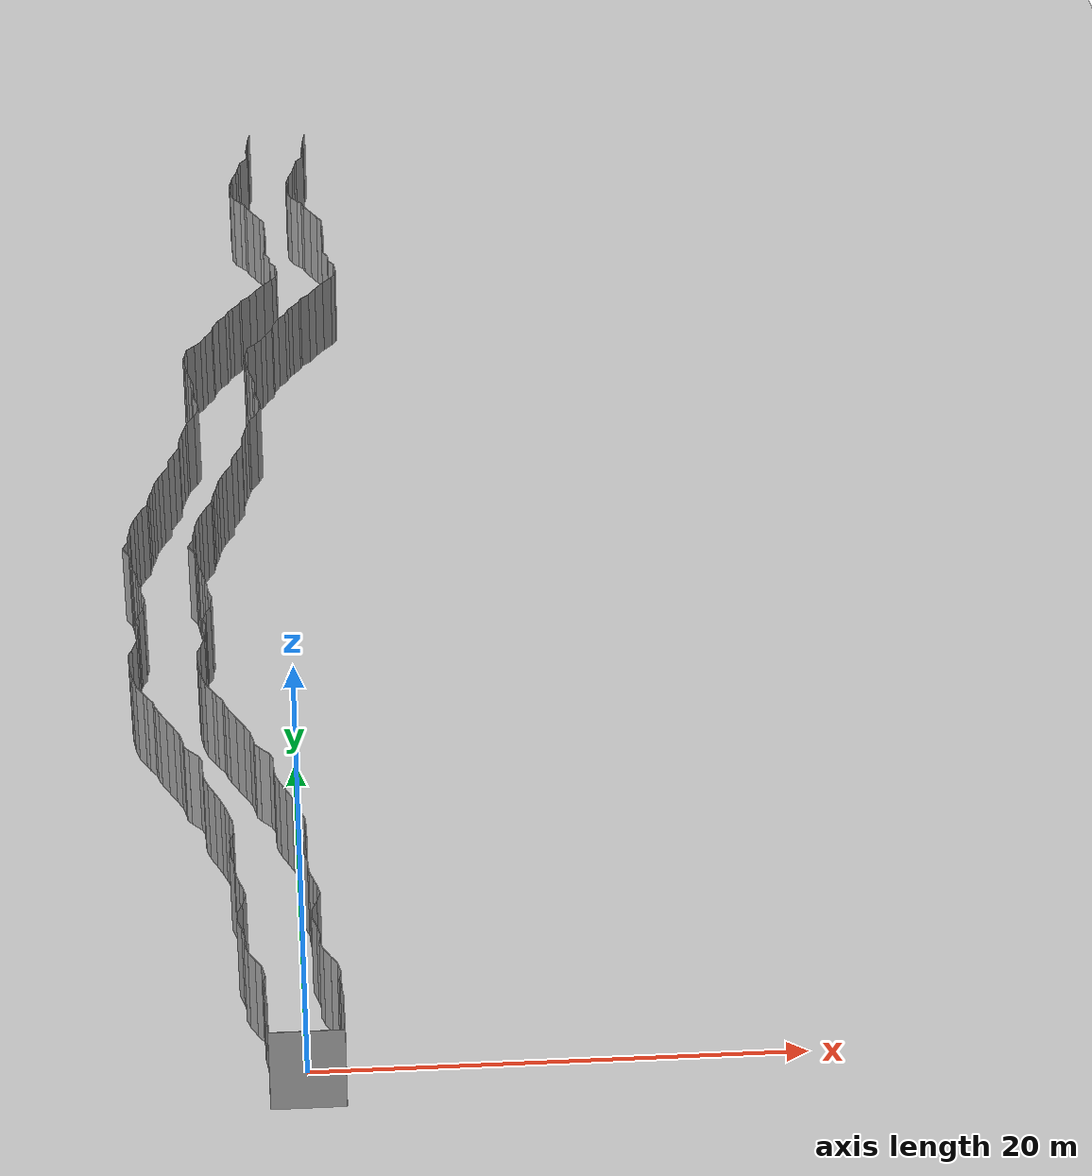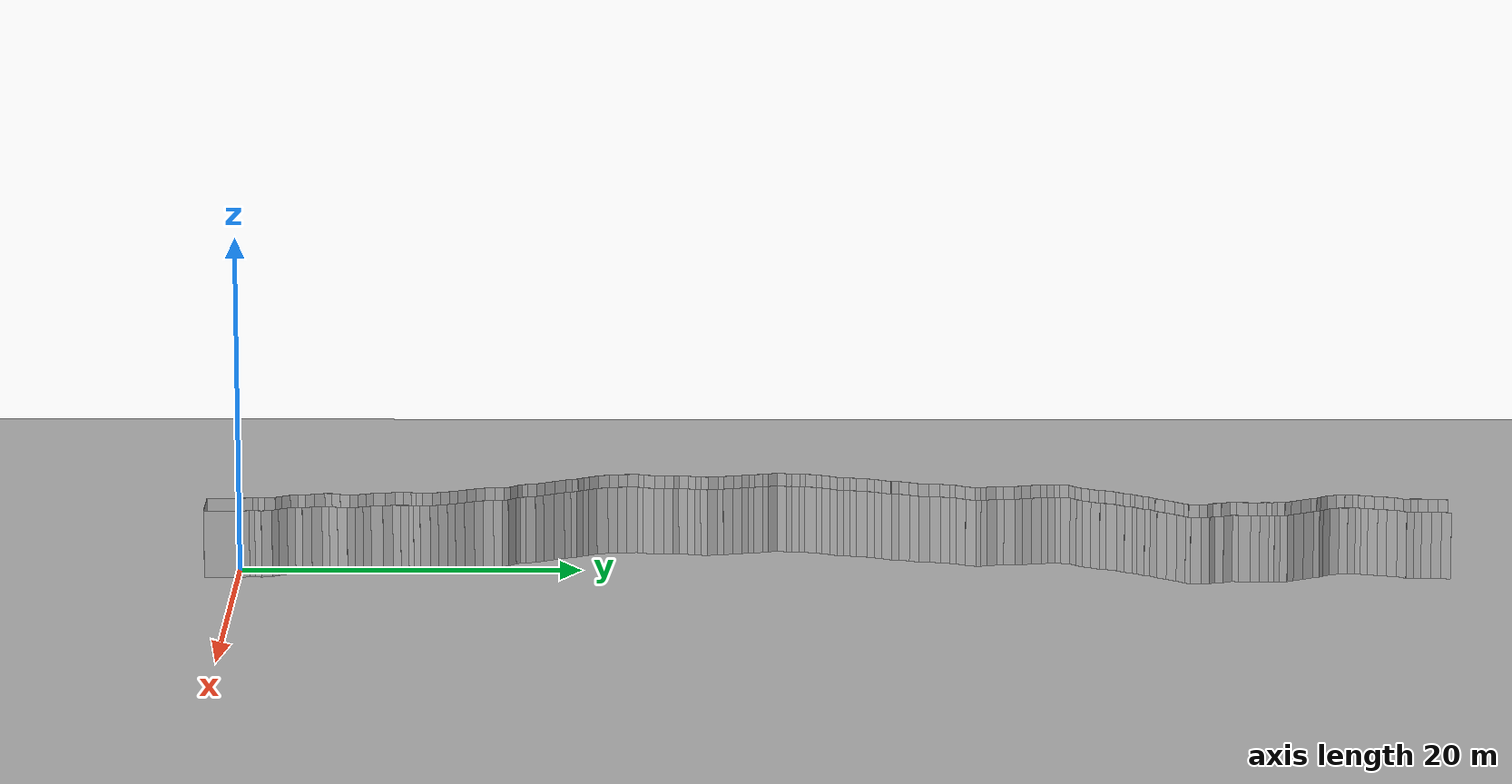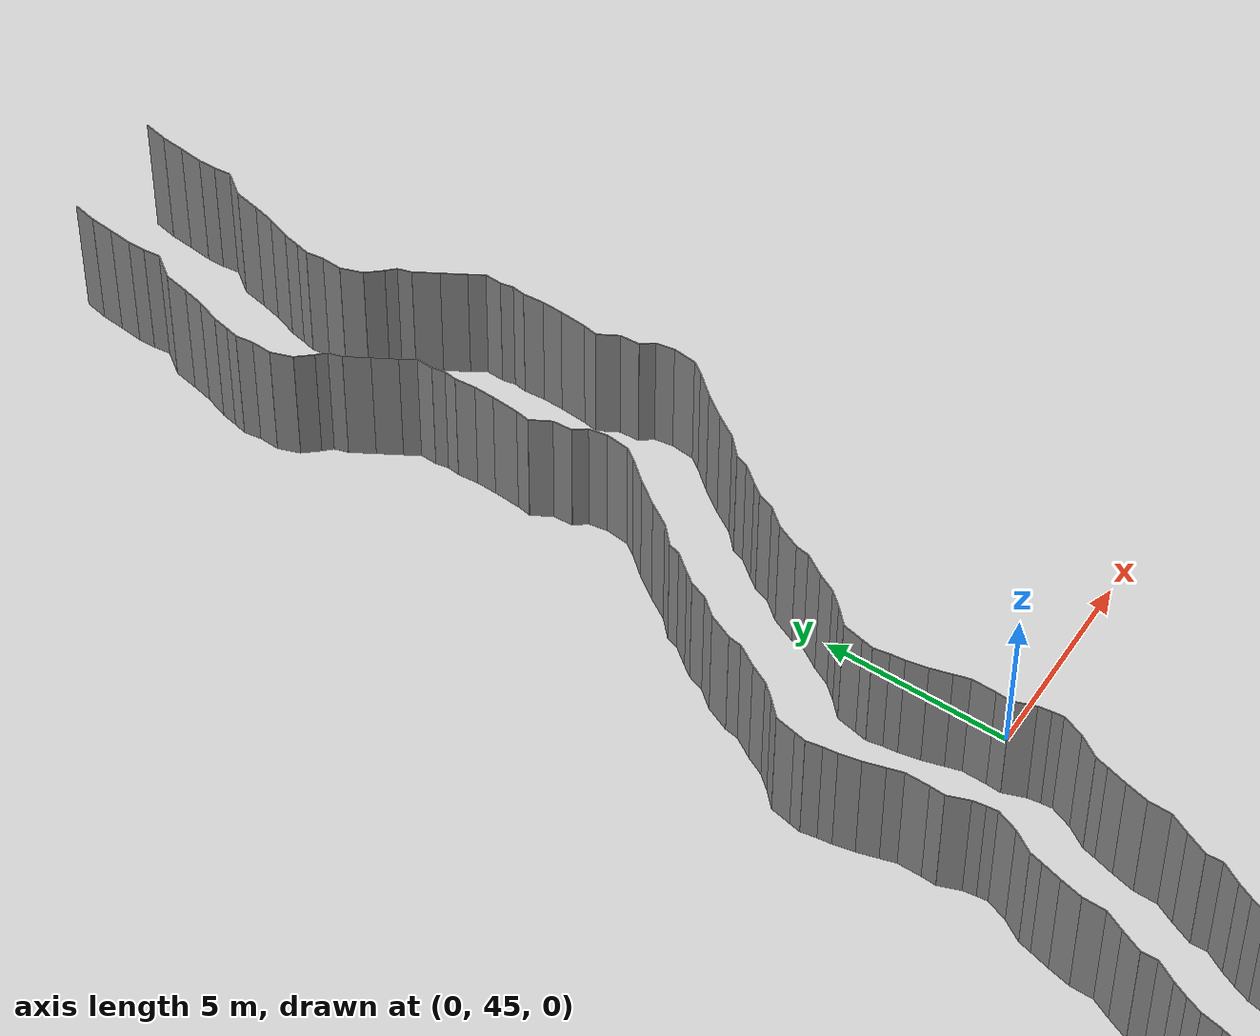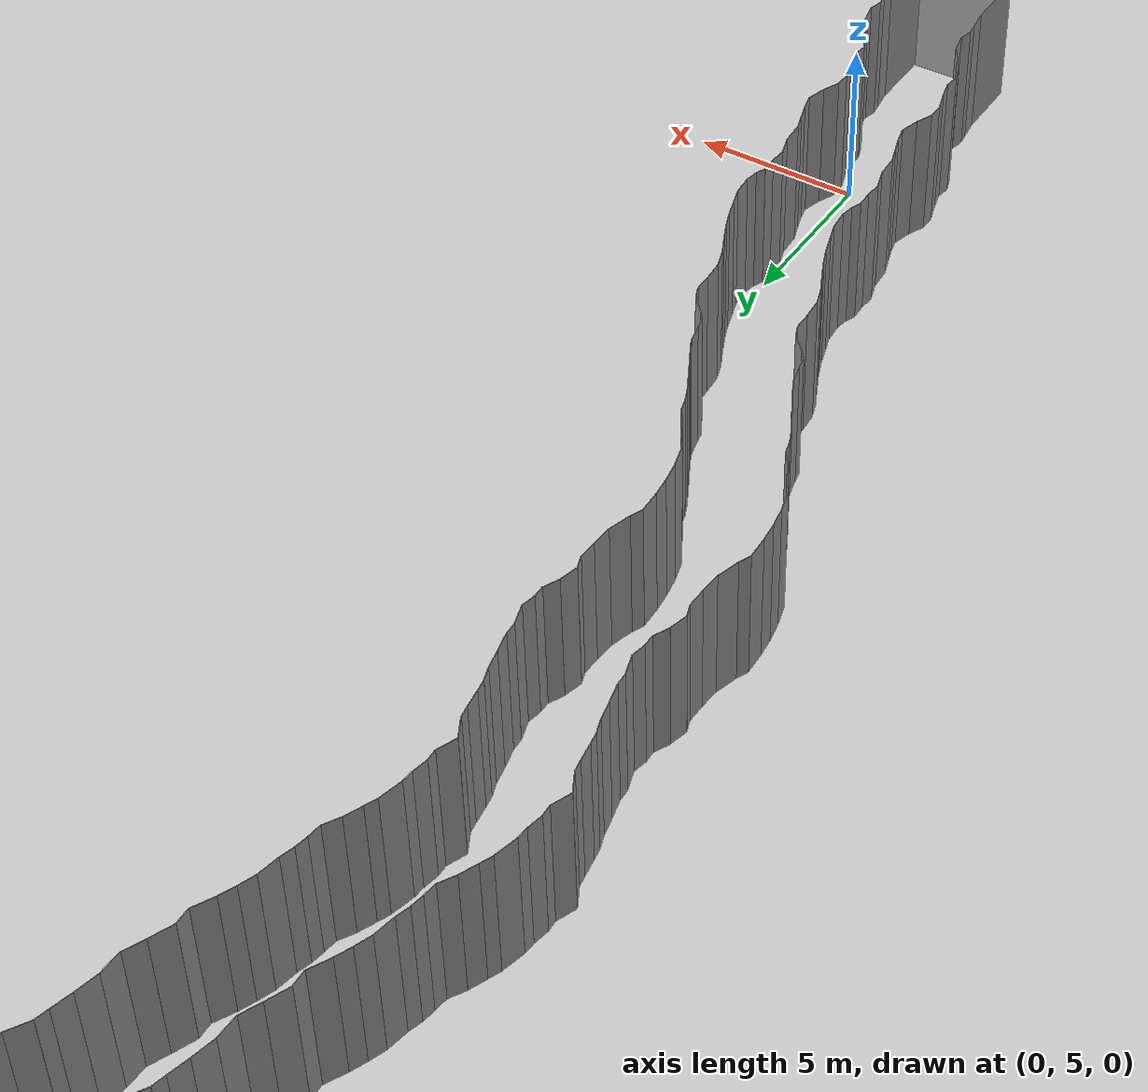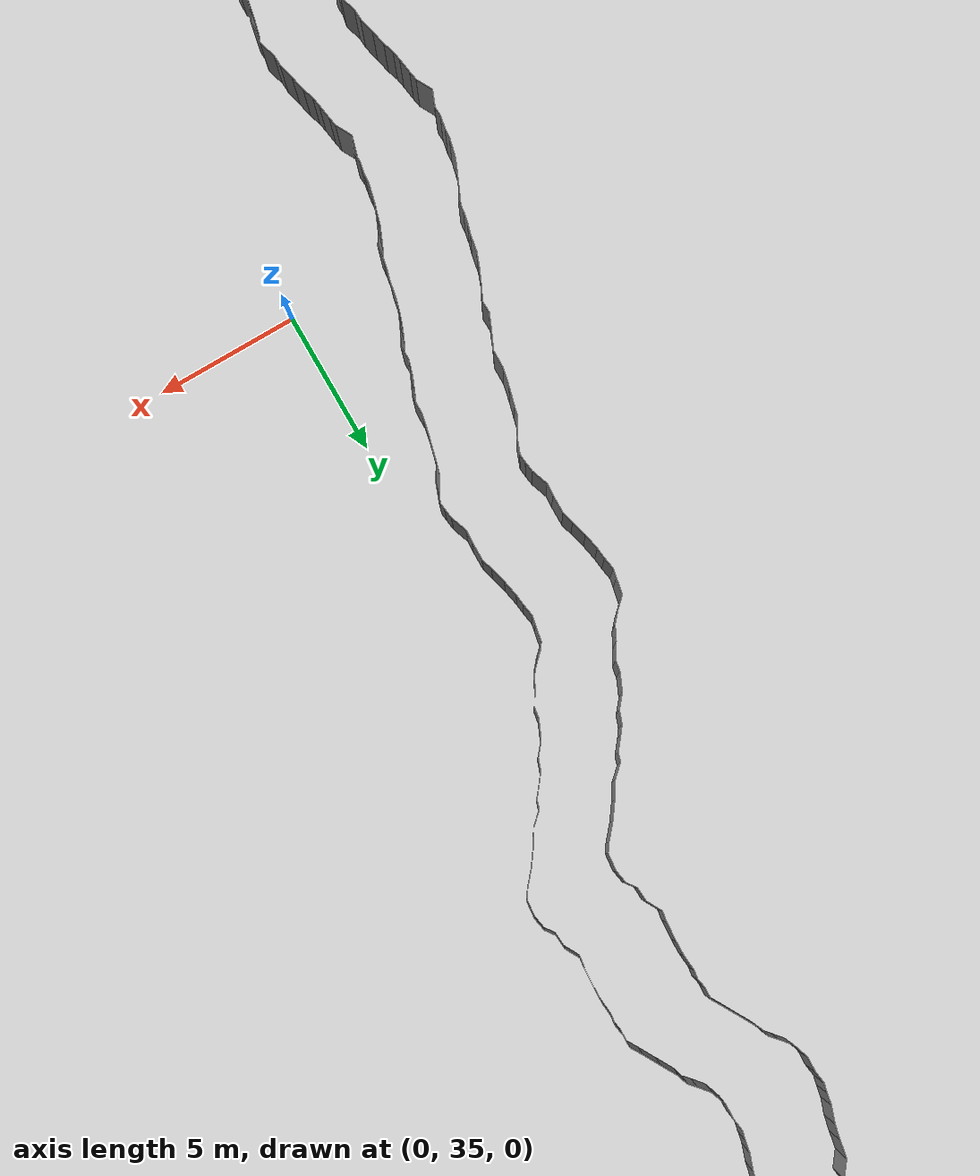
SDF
<sdf version="1.6">
 <world name="default">
  <light name="sun" type="directional">
   <pose>0 0 10 0 -0 0</pose>
   <diffuse>0.8 0.8 0.8 1</diffuse>
   <specular>0.2 0.2 0.2 1</specular>
   <attenuation>
    <range>1000</range>
    <constant>0.9</constant>
    <linear>0.01</linear>
    <quadratic>0.001</quadratic>
   </attenuation>
   <direction>-0.5 0.1 -0.9</direction>
  </light>
  <model name="ground_plane">
   <static>1</static>
   <link name="link">
    <collision name="collision">
     <geometry><plane><normal>0 0 1</normal><size>200 200</size></plane></geometry>
     <surface><friction><ode><mu>100</mu><mu2>50</mu2></ode></friction></surface>
    </collision>
    <visual name="visual">
     <cast_shadows>0</cast_shadows>
     <geometry><plane><normal>0 0 1</normal><size>200 200</size></plane></geometry>
     <material>
      <script><uri>file://media/materials/scripts/gazebo.material</uri><name>Gazebo/Grey</name></script>
     </material>
    </visual>
   </link>
   <pose>0 100 0 0 -0 0</pose>
  </model>
  <gravity>0 0 -9.8</gravity>
  <magnetic_field>6e-06 2.3e-05 -4.2e-05</magnetic_field>
  <atmosphere type="adiabatic"/>
  <physics default="0" name="default_physics" type="ode">
   <max_step_size>0.001</max_step_size>
   <real_time_factor>1</real_time_factor>
   <real_time_update_rate>1000</real_time_update_rate>
  </physics>
  <scene><ambient>0.4 0.4 0.4 1</ambient><background>0.7 0.7 0.7 1</background><shadows>1</shadows></scene>
  <spherical_coordinates>
   <surface_model>EARTH_WGS84</surface_model>
   <latitude_deg>0</latitude_deg>
   <longitude_deg>0</longitude_deg>
   <elevation>0</elevation>
   <heading_deg>0</heading_deg>
  </spherical_coordinates>
  <model name="wall_back">
   <static>1</static>
   <pose>0.0 -2 2 0.0 0 0.0</pose>
   <link name="link">
    <collision name="collision"><geometry><box><size>3 0.02 4</size></box></geometry></collision>
    <visual name="visual">
     <material>
      <script><name>Gazebo/Grey</name><uri>file://media/materials/scripts/gazebo.material</uri></script>
     </material>
     <geometry><box><size>3 0.02 4</size></box></geometry>
    </visual>
   </link>
  </model>
  <model name="wall_left">
   <static>1</static>
   <pose>1.5 -1 2 0 0 0.00</pose>
   <link name="link">
    <collision name="collision"><geometry><box><size>0.02 2 4</size></box></geometry></collision>
    <visual name="visual">
     <material>
      <script><name>Gazebo/Grey</name><uri>file://media/materials/scripts/gazebo.material</uri></script>
     </material>
     <geometry><box><size>0.02 2 4</size></box></geometry>
    </visual>
   </link>
  </model>
  <model name="wall_right">
   <static>1</static>
   <pose>-1.5 -1 2 0 0 0.00</pose>
   <link name="link">
    <collision name="collision"><geometry><box><size>0.02 2 4</size></box></geometry></collision>
    <visual name="visual">
     <material>
      <script><name>Gazebo/Grey</name><uri>file://media/materials/scripts/gazebo.material</uri></script>
     </material>
     <geometry><box><size>0.02 2 4</size></box></geometry>
    </visual>
   </link>
  </model>
  <model name="wall_0">
   <static>1</static>
   <pose>-1.5460609407152022 0.32296351632783216 2 0 0 0.1416642949289696</pose>
   <link name="link">
    <collision name="collision"><geometry><box><size>0.02 0.652463158005 4</size></box></geometry></collision>
    <visual name="visual">
     <material>
      <script><name>Gazebo/Grey</name><uri>file://media/materials/scripts/gazebo.material</uri></script>
     </material>
     <geometry><box><size>0.02 0.652463158005 4</size></box></geometry>
    </visual>
   </link>
  </model>
  <model name="wall_1">
   <static>1</static>
   <pose>1.4539390592847978 0.32296351632783216 2 0 0 0.1416642949289696</pose>
   <link name="link">
    <collision name="collision"><geometry><box><size>0.02 0.652463158005 4</size></box></geometry></collision>
    <visual name="visual">
     <material>
      <script><name>Gazebo/Grey</name><uri>file://media/materials/scripts/gazebo.material</uri></script>
     </material>
     <geometry><box><size>0.02 0.652463158005 4</size></box></geometry>
    </visual>
   </link>
  </model>
  <model name="wall_2">
   <static>1</static>
   <pose>-1.6148269686521954 0.8086788979498543 2 0 0 0.13861276403303396</pose>
   <link name="link">
    <collision name="collision"><geometry><box><size>0.02 0.328655994271 4</size></box></geometry></collision>
    <visual name="visual">
     <material>
      <script><name>Gazebo/Grey</name><uri>file://media/materials/scripts/gazebo.material</uri></script>
     </material>
     <geometry><box><size>0.02 0.328655994271 4</size></box></geometry>
    </visual>
   </link>
  </model>
  <model name="wall_3">
   <static>1</static>
   <pose>1.3851730313478046 0.8086788979498543 2 0 0 0.13861276403303396</pose>
   <link name="link">
    <collision name="collision"><geometry><box><size>0.02 0.328655994271 4</size></box></geometry></collision>
    <visual name="visual">
     <material>
      <script><name>Gazebo/Grey</name><uri>file://media/materials/scripts/gazebo.material</uri></script>
     </material>
     <geometry><box><size>0.02 0.328655994271 4</size></box></geometry>
    </visual>
   </link>
  </model>
  <model name="wall_4">
   <static>1</static>
   <pose>-1.589722143437449 1.1666687135756386 2 0 0 -0.24015427331830977</pose>
   <link name="link">
    <collision name="collision"><geometry><box><size>0.02 0.402013158874 4</size></box></geometry></collision>
    <visual name="visual">
     <material>
      <script><name>Gazebo/Grey</name><uri>file://media/materials/scripts/gazebo.material</uri></script>
     </material>
     <geometry><box><size>0.02 0.402013158874 4</size></box></geometry>
    </visual>
   </link>
  </model>
  <model name="wall_5">
   <static>1</static>
   <pose>1.410277856562551 1.1666687135756386 2 0 0 -0.24015427331830977</pose>
   <link name="link">
    <collision name="collision"><geometry><box><size>0.02 0.402013158874 4</size></box></geometry></collision>
    <visual name="visual">
     <material>
      <script><name>Gazebo/Grey</name><uri>file://media/materials/scripts/gazebo.material</uri></script>
     </material>
     <geometry><box><size>0.02 0.402013158874 4</size></box></geometry>
    </visual>
   </link>
  </model>
  <model name="wall_6">
   <static>1</static>
   <pose>-1.6083255179823068 1.6642239231955354 2 0 0 0.21624578785075813</pose>
   <link name="link">
    <collision name="collision"><geometry><box><size>0.02 0.619052340118 4</size></box></geometry></collision>
    <visual name="visual">
     <material>
      <script><name>Gazebo/Grey</name><uri>file://media/materials/scripts/gazebo.material</uri></script>
     </material>
     <geometry><box><size>0.02 0.619052340118 4</size></box></geometry>
    </visual>
   </link>
  </model>
  <model name="wall_7">
   <static>1</static>
   <pose>1.3916744820176932 1.6642239231955354 2 0 0 0.21624578785075813</pose>
   <link name="link">
    <collision name="collision"><geometry><box><size>0.02 0.619052340118 4</size></box></geometry></collision>
    <visual name="visual">
     <material>
      <script><name>Gazebo/Grey</name><uri>file://media/materials/scripts/gazebo.material</uri></script>
     </material>
     <geometry><box><size>0.02 0.619052340118 4</size></box></geometry>
    </visual>
   </link>
  </model>
  <model name="wall_8">
   <static>1</static>
   <pose>-1.7974376571716444 2.155563262179853 2 0 0 0.5757594685593171</pose>
   <link name="link">
    <collision name="collision"><geometry><box><size>0.02 0.450707687735 4</size></box></geometry></collision>
    <visual name="visual">
     <material>
      <script><name>Gazebo/Grey</name><uri>file://media/materials/scripts/gazebo.material</uri></script>
     </material>
     <geometry><box><size>0.02 0.450707687735 4</size></box></geometry>
    </visual>
   </link>
  </model>
  <model name="wall_9">
   <static>1</static>
   <pose>1.2025623428283556 2.155563262179853 2 0 0 0.5757594685593171</pose>
   <link name="link">
    <collision name="collision"><geometry><box><size>0.02 0.450707687735 4</size></box></geometry></collision>
    <visual name="visual">
     <material>
      <script><name>Gazebo/Grey</name><uri>file://media/materials/scripts/gazebo.material</uri></script>
     </material>
     <geometry><box><size>0.02 0.450707687735 4</size></box></geometry>
    </visual>
   </link>
  </model>
  <model name="wall_10">
   <static>1</static>
   <pose>-2.060361808506583 2.589705850131935 2 0 0 0.5196270907715346</pose>
   <link name="link">
    <collision name="collision"><geometry><box><size>0.02 0.564790927983 4</size></box></geometry></collision>
    <visual name="visual">
     <material>
      <script><name>Gazebo/Grey</name><uri>file://media/materials/scripts/gazebo.material</uri></script>
     </material>
     <geometry><box><size>0.02 0.564790927983 4</size></box></geometry>
    </visual>
   </link>
  </model>
  <model name="wall_11">
   <static>1</static>
   <pose>0.9396381914934171 2.589705850131935 2 0 0 0.5196270907715346</pose>
   <link name="link">
    <collision name="collision"><geometry><box><size>0.02 0.564790927983 4</size></box></geometry></collision>
    <visual name="visual">
     <material>
      <script><name>Gazebo/Grey</name><uri>file://media/materials/scripts/gazebo.material</uri></script>
     </material>
     <geometry><box><size>0.02 0.564790927983 4</size></box></geometry>
    </visual>
   </link>
  </model>
  <model name="wall_12">
   <static>1</static>
   <pose>-2.277429173906964 3.0615047364817056 2 0 0 0.32683432171715104</pose>
   <link name="link">
    <collision name="collision"><geometry><box><size>0.02 0.47869735844 4</size></box></geometry></collision>
    <visual name="visual">
     <material>
      <script><name>Gazebo/Grey</name><uri>file://media/materials/scripts/gazebo.material</uri></script>
     </material>
     <geometry><box><size>0.02 0.47869735844 4</size></box></geometry>
    </visual>
   </link>
  </model>
  <model name="wall_13">
   <static>1</static>
   <pose>0.7225708260930359 3.0615047364817056 2 0 0 0.32683432171715104</pose>
   <link name="link">
    <collision name="collision"><geometry><box><size>0.02 0.47869735844 4</size></box></geometry></collision>
    <visual name="visual">
     <material>
      <script><name>Gazebo/Grey</name><uri>file://media/materials/scripts/gazebo.material</uri></script>
     </material>
     <geometry><box><size>0.02 0.47869735844 4</size></box></geometry>
    </visual>
   </link>
  </model>
  <model name="wall_14">
   <static>1</static>
   <pose>-2.3266724309295896 3.4999744161331265 2 0 0 -0.12958116203599063</pose>
   <link name="link">
    <collision name="collision"><geometry><box><size>0.02 0.427163901507 4</size></box></geometry></collision>
    <visual name="visual">
     <material>
      <script><name>Gazebo/Grey</name><uri>file://media/materials/scripts/gazebo.material</uri></script>
     </material>
     <geometry><box><size>0.02 0.427163901507 4</size></box></geometry>
    </visual>
   </link>
  </model>
  <model name="wall_15">
   <static>1</static>
   <pose>0.6733275690704104 3.4999744161331265 2 0 0 -0.12958116203599063</pose>
   <link name="link">
    <collision name="collision"><geometry><box><size>0.02 0.427163901507 4</size></box></geometry></collision>
    <visual name="visual">
     <material>
      <script><name>Gazebo/Grey</name><uri>file://media/materials/scripts/gazebo.material</uri></script>
     </material>
     <geometry><box><size>0.02 0.427163901507 4</size></box></geometry>
    </visual>
   </link>
  </model>
  <model name="wall_16">
   <static>1</static>
   <pose>-2.3666623829114717 3.9763269958883276 2 0 0 0.2501248180982221</pose>
   <link name="link">
    <collision name="collision"><geometry><box><size>0.02 0.546116876013 4</size></box></geometry></collision>
    <visual name="visual">
     <material>
      <script><name>Gazebo/Grey</name><uri>file://media/materials/scripts/gazebo.material</uri></script>
     </material>
     <geometry><box><size>0.02 0.546116876013 4</size></box></geometry>
    </visual>
   </link>
  </model>
  <model name="wall_17">
   <static>1</static>
   <pose>0.6333376170885283 3.9763269958883276 2 0 0 0.2501248180982221</pose>
   <link name="link">
    <collision name="collision"><geometry><box><size>0.02 0.546116876013 4</size></box></geometry></collision>
    <visual name="visual">
     <material>
      <script><name>Gazebo/Grey</name><uri>file://media/materials/scripts/gazebo.material</uri></script>
     </material>
     <geometry><box><size>0.02 0.546116876013 4</size></box></geometry>
    </visual>
   </link>
  </model>
  <model name="wall_18">
   <static>1</static>
   <pose>-2.528932439089104 4.541833459454673 2 0 0 0.3048088020196074</pose>
   <link name="link">
    <collision name="collision"><geometry><box><size>0.02 0.630975600825 4</size></box></geometry></collision>
    <visual name="visual">
     <material>
      <script><name>Gazebo/Grey</name><uri>file://media/materials/scripts/gazebo.material</uri></script>
     </material>
     <geometry><box><size>0.02 0.630975600825 4</size></box></geometry>
    </visual>
   </link>
  </model>
  <model name="wall_19">
   <static>1</static>
   <pose>0.4710675609108961 4.541833459454673 2 0 0 0.3048088020196074</pose>
   <link name="link">
    <collision name="collision"><geometry><box><size>0.02 0.630975600825 4</size></box></geometry></collision>
    <visual name="visual">
     <material>
      <script><name>Gazebo/Grey</name><uri>file://media/materials/scripts/gazebo.material</uri></script>
     </material>
     <geometry><box><size>0.02 0.630975600825 4</size></box></geometry>
    </visual>
   </link>
  </model>
  <model name="wall_20">
   <static>1</static>
   <pose>-2.6120455961579236 5.0558911683536 2 0 0 -0.05422861042586933</pose>
   <link name="link">
    <collision name="collision"><geometry><box><size>0.02 0.426852524881 4</size></box></geometry></collision>
    <visual name="visual">
     <material>
      <script><name>Gazebo/Grey</name><uri>file://media/materials/scripts/gazebo.material</uri></script>
     </material>
     <geometry><box><size>0.02 0.426852524881 4</size></box></geometry>
    </visual>
   </link>
  </model>
  <model name="wall_21">
   <static>1</static>
   <pose>0.38795440384207636 5.0558911683536 2 0 0 -0.05422861042586933</pose>
   <link name="link">
    <collision name="collision"><geometry><box><size>0.02 0.426852524881 4</size></box></geometry></collision>
    <visual name="visual">
     <material>
      <script><name>Gazebo/Grey</name><uri>file://media/materials/scripts/gazebo.material</uri></script>
     </material>
     <geometry><box><size>0.02 0.426852524881 4</size></box></geometry>
    </visual>
   </link>
  </model>
  <model name="wall_22">
   <static>1</static>
   <pose>-2.494607655139422 5.517572227282669 2 0 0 -0.4026479095443458</pose>
   <link name="link">
    <collision name="collision"><geometry><box><size>0.02 0.540350745379 4</size></box></geometry></collision>
    <visual name="visual">
     <material>
      <script><name>Gazebo/Grey</name><uri>file://media/materials/scripts/gazebo.material</uri></script>
     </material>
     <geometry><box><size>0.02 0.540350745379 4</size></box></geometry>
    </visual>
   </link>
  </model>
  <model name="wall_23">
   <static>1</static>
   <pose>0.5053923448605779 5.517572227282669 2 0 0 -0.4026479095443458</pose>
   <link name="link">
    <collision name="collision"><geometry><box><size>0.02 0.540350745379 4</size></box></geometry></collision>
    <visual name="visual">
     <material>
      <script><name>Gazebo/Grey</name><uri>file://media/materials/scripts/gazebo.material</uri></script>
     </material>
     <geometry><box><size>0.02 0.540350745379 4</size></box></geometry>
    </visual>
   </link>
  </model>
  <model name="wall_24">
   <static>1</static>
   <pose>-2.312584351391815 6.052139907059537 2 0 0 -0.26023368327982066</pose>
   <link name="link">
    <collision name="collision"><geometry><box><size>0.02 0.591928597854 4</size></box></geometry></collision>
    <visual name="visual">
     <material>
      <script><name>Gazebo/Grey</name><uri>file://media/materials/scripts/gazebo.material</uri></script>
     </material>
     <geometry><box><size>0.02 0.591928597854 4</size></box></geometry>
    </visual>
   </link>
  </model>
  <model name="wall_25">
   <static>1</static>
   <pose>0.687415648608185 6.052139907059537 2 0 0 -0.26023368327982066</pose>
   <link name="link">
    <collision name="collision"><geometry><box><size>0.02 0.591928597854 4</size></box></geometry></collision>
    <visual name="visual">
     <material>
      <script><name>Gazebo/Grey</name><uri>file://media/materials/scripts/gazebo.material</uri></script>
     </material>
     <geometry><box><size>0.02 0.591928597854 4</size></box></geometry>
    </visual>
   </link>
  </model>
  <model name="wall_26">
   <static>1</static>
   <pose>-2.29260806861817 6.564511362398333 2 0 0 0.24324891789638955</pose>
   <link name="link">
    <collision name="collision"><geometry><box><size>0.02 0.466477450572 4</size></box></geometry></collision>
    <visual name="visual">
     <material>
      <script><name>Gazebo/Grey</name><uri>file://media/materials/scripts/gazebo.material</uri></script>
     </material>
     <geometry><box><size>0.02 0.466477450572 4</size></box></geometry>
    </visual>
   </link>
  </model>
  <model name="wall_27">
   <static>1</static>
   <pose>0.7073919313818302 6.564511362398333 2 0 0 0.24324891789638955</pose>
   <link name="link">
    <collision name="collision"><geometry><box><size>0.02 0.466477450572 4</size></box></geometry></collision>
    <visual name="visual">
     <material>
      <script><name>Gazebo/Grey</name><uri>file://media/materials/scripts/gazebo.material</uri></script>
     </material>
     <geometry><box><size>0.02 0.466477450572 4</size></box></geometry>
    </visual>
   </link>
  </model>
  <model name="wall_28">
   <static>1</static>
   <pose>-2.4247002136703846 7.022733952686844 2 0 0 0.3164289197949313</pose>
   <link name="link">
    <collision name="collision"><geometry><box><size>0.02 0.487924699925 4</size></box></geometry></collision>
    <visual name="visual">
     <material>
      <script><name>Gazebo/Grey</name><uri>file://media/materials/scripts/gazebo.material</uri></script>
     </material>
     <geometry><box><size>0.02 0.487924699925 4</size></box></geometry>
    </visual>
   </link>
  </model>
  <model name="wall_29">
   <static>1</static>
   <pose>0.5752997863296154 7.022733952686844 2 0 0 0.3164289197949313</pose>
   <link name="link">
    <collision name="collision"><geometry><box><size>0.02 0.487924699925 4</size></box></geometry></collision>
    <visual name="visual">
     <material>
      <script><name>Gazebo/Grey</name><uri>file://media/materials/scripts/gazebo.material</uri></script>
     </material>
     <geometry><box><size>0.02 0.487924699925 4</size></box></geometry>
    </visual>
   </link>
  </model>
  <model name="wall_30">
   <static>1</static>
   <pose>-2.57577664151554 7.4826767092342115 2 0 0 0.31831648618734026</pose>
   <link name="link">
    <collision name="collision"><geometry><box><size>0.02 0.480314186092 4</size></box></geometry></collision>
    <visual name="visual">
     <material>
      <script><name>Gazebo/Grey</name><uri>file://media/materials/scripts/gazebo.material</uri></script>
     </material>
     <geometry><box><size>0.02 0.480314186092 4</size></box></geometry>
    </visual>
   </link>
  </model>
  <model name="wall_31">
   <static>1</static>
   <pose>0.4242233584844599 7.4826767092342115 2 0 0 0.31831648618734026</pose>
   <link name="link">
    <collision name="collision"><geometry><box><size>0.02 0.480314186092 4</size></box></geometry></collision>
    <visual name="visual">
     <material>
      <script><name>Gazebo/Grey</name><uri>file://media/materials/scripts/gazebo.material</uri></script>
     </material>
     <geometry><box><size>0.02 0.480314186092 4</size></box></geometry>
    </visual>
   </link>
  </model>
  <model name="wall_32">
   <static>1</static>
   <pose>-2.6733809807644473 8.05867889216944 2 0 0 0.0644183986733915</pose>
   <link name="link">
    <collision name="collision"><geometry><box><size>0.02 0.697265643314 4</size></box></geometry></collision>
    <visual name="visual">
     <material>
      <script><name>Gazebo/Grey</name><uri>file://media/materials/scripts/gazebo.material</uri></script>
     </material>
     <geometry><box><size>0.02 0.697265643314 4</size></box></geometry>
    </visual>
   </link>
  </model>
  <model name="wall_33">
   <static>1</static>
   <pose>0.3266190192355527 8.05867889216944 2 0 0 0.0644183986733915</pose>
   <link name="link">
    <collision name="collision"><geometry><box><size>0.02 0.697265643314 4</size></box></geometry></collision>
    <visual name="visual">
     <material>
      <script><name>Gazebo/Grey</name><uri>file://media/materials/scripts/gazebo.material</uri></script>
     </material>
     <geometry><box><size>0.02 0.697265643314 4</size></box></geometry>
    </visual>
   </link>
  </model>
  <model name="wall_34">
   <static>1</static>
   <pose>-2.787935674579615 8.689447104098766 2 0 0 0.3148164376250054</pose>
   <link name="link">
    <collision name="collision"><geometry><box><size>0.02 0.594957236797 4</size></box></geometry></collision>
    <visual name="visual">
     <material>
      <script><name>Gazebo/Grey</name><uri>file://media/materials/scripts/gazebo.material</uri></script>
     </material>
     <geometry><box><size>0.02 0.594957236797 4</size></box></geometry>
    </visual>
   </link>
  </model>
  <model name="wall_35">
   <static>1</static>
   <pose>0.2120643254203851 8.689447104098766 2 0 0 0.3148164376250054</pose>
   <link name="link">
    <collision name="collision"><geometry><box><size>0.02 0.594957236797 4</size></box></geometry></collision>
    <visual name="visual">
     <material>
      <script><name>Gazebo/Grey</name><uri>file://media/materials/scripts/gazebo.material</uri></script>
     </material>
     <geometry><box><size>0.02 0.594957236797 4</size></box></geometry>
    </visual>
   </link>
  </model>
  <model name="wall_36">
   <static>1</static>
   <pose>-2.8603803701452333 9.20700265309586 2 0 0 -0.08360274740637143</pose>
   <link name="link">
    <collision name="collision"><geometry><box><size>0.02 0.471039272498 4</size></box></geometry></collision>
    <visual name="visual">
     <material>
      <script><name>Gazebo/Grey</name><uri>file://media/materials/scripts/gazebo.material</uri></script>
     </material>
     <geometry><box><size>0.02 0.471039272498 4</size></box></geometry>
    </visual>
   </link>
  </model>
  <model name="wall_37">
   <static>1</static>
   <pose>0.13961962985476672 9.20700265309586 2 0 0 -0.08360274740637143</pose>
   <link name="link">
    <collision name="collision"><geometry><box><size>0.02 0.471039272498 4</size></box></geometry></collision>
    <visual name="visual">
     <material>
      <script><name>Gazebo/Grey</name><uri>file://media/materials/scripts/gazebo.material</uri></script>
     </material>
     <geometry><box><size>0.02 0.471039272498 4</size></box></geometry>
    </visual>
   </link>
  </model>
  <model name="wall_38">
   <static>1</static>
   <pose>-2.849914418016406 9.676256551270113 2 0 0 0.03920794430056313</pose>
   <link name="link">
    <collision name="collision"><geometry><box><size>0.02 0.469474517436 4</size></box></geometry></collision>
    <visual name="visual">
     <material>
      <script><name>Gazebo/Grey</name><uri>file://media/materials/scripts/gazebo.material</uri></script>
     </material>
     <geometry><box><size>0.02 0.469474517436 4</size></box></geometry>
    </visual>
   </link>
  </model>
  <model name="wall_39">
   <static>1</static>
   <pose>0.150085581983594 9.676256551270113 2 0 0 0.03920794430056313</pose>
   <link name="link">
    <collision name="collision"><geometry><box><size>0.02 0.469474517436 4</size></box></geometry></collision>
    <visual name="visual">
     <material>
      <script><name>Gazebo/Grey</name><uri>file://media/materials/scripts/gazebo.material</uri></script>
     </material>
     <geometry><box><size>0.02 0.469474517436 4</size></box></geometry>
    </visual>
   </link>
  </model>
  <model name="wall_40">
   <static>1</static>
   <pose>-2.799212834921208 10.056202752280775 2 0 0 -0.3908222059121269</pose>
   <link name="link">
    <collision name="collision"><geometry><box><size>0.02 0.314492646276 4</size></box></geometry></collision>
    <visual name="visual">
     <material>
      <script><name>Gazebo/Grey</name><uri>file://media/materials/scripts/gazebo.material</uri></script>
     </material>
     <geometry><box><size>0.02 0.314492646276 4</size></box></geometry>
    </visual>
   </link>
  </model>
  <model name="wall_41">
   <static>1</static>
   <pose>0.20078716507879202 10.056202752280775 2 0 0 -0.3908222059121269</pose>
   <link name="link">
    <collision name="collision"><geometry><box><size>0.02 0.314492646276 4</size></box></geometry></collision>
    <visual name="visual">
     <material>
      <script><name>Gazebo/Grey</name><uri>file://media/materials/scripts/gazebo.material</uri></script>
     </material>
     <geometry><box><size>0.02 0.314492646276 4</size></box></geometry>
    </visual>
   </link>
  </model>
  <model name="wall_42">
   <static>1</static>
   <pose>-2.710360181657193 10.393337643875538 2 0 0 -0.1498488573550786</pose>
   <link name="link">
    <collision name="collision"><geometry><box><size>0.02 0.387837331623 4</size></box></geometry></collision>
    <visual name="visual">
     <material>
      <script><name>Gazebo/Grey</name><uri>file://media/materials/scripts/gazebo.material</uri></script>
     </material>
     <geometry><box><size>0.02 0.387837331623 4</size></box></geometry>
    </visual>
   </link>
  </model>
  <model name="wall_43">
   <static>1</static>
   <pose>0.28963981834280705 10.393337643875538 2 0 0 -0.1498488573550786</pose>
   <link name="link">
    <collision name="collision"><geometry><box><size>0.02 0.387837331623 4</size></box></geometry></collision>
    <visual name="visual">
     <material>
      <script><name>Gazebo/Grey</name><uri>file://media/materials/scripts/gazebo.material</uri></script>
     </material>
     <geometry><box><size>0.02 0.387837331623 4</size></box></geometry>
    </visual>
   </link>
  </model>
  <model name="wall_44">
   <static>1</static>
   <pose>-2.70590756374895 10.877294180496323 2 0 0 0.08363852214404005</pose>
   <link name="link">
    <collision name="collision"><geometry><box><size>0.02 0.586472089891 4</size></box></geometry></collision>
    <visual name="visual">
     <material>
      <script><name>Gazebo/Grey</name><uri>file://media/materials/scripts/gazebo.material</uri></script>
     </material>
     <geometry><box><size>0.02 0.586472089891 4</size></box></geometry>
    </visual>
   </link>
  </model>
  <model name="wall_45">
   <static>1</static>
   <pose>0.29409243625104997 10.877294180496323 2 0 0 0.08363852214404005</pose>
   <link name="link">
    <collision name="collision"><geometry><box><size>0.02 0.586472089891 4</size></box></geometry></collision>
    <visual name="visual">
     <material>
      <script><name>Gazebo/Grey</name><uri>file://media/materials/scripts/gazebo.material</uri></script>
     </material>
     <geometry><box><size>0.02 0.586472089891 4</size></box></geometry>
    </visual>
   </link>
  </model>
  <model name="wall_46">
   <static>1</static>
   <pose>-2.805017338441254 11.402402055324732 2 0 0 0.3100360287135226</pose>
   <link name="link">
    <collision name="collision"><geometry><box><size>0.02 0.489113435858 4</size></box></geometry></collision>
    <visual name="visual">
     <material>
      <script><name>Gazebo/Grey</name><uri>file://media/materials/scripts/gazebo.material</uri></script>
     </material>
     <geometry><box><size>0.02 0.489113435858 4</size></box></geometry>
    </visual>
   </link>
  </model>
  <model name="wall_47">
   <static>1</static>
   <pose>0.194982661558746 11.402402055324732 2 0 0 0.3100360287135226</pose>
   <link name="link">
    <collision name="collision"><geometry><box><size>0.02 0.489113435858 4</size></box></geometry></collision>
    <visual name="visual">
     <material>
      <script><name>Gazebo/Grey</name><uri>file://media/materials/scripts/gazebo.material</uri></script>
     </material>
     <geometry><box><size>0.02 0.489113435858 4</size></box></geometry>
    </visual>
   </link>
  </model>
  <model name="wall_48">
   <static>1</static>
   <pose>-2.963712063873502 11.900903078463639 2 0 0 0.30658809499920986</pose>
   <link name="link">
    <collision name="collision"><geometry><box><size>0.02 0.557190718628 4</size></box></geometry></collision>
    <visual name="visual">
     <material>
      <script><name>Gazebo/Grey</name><uri>file://media/materials/scripts/gazebo.material</uri></script>
     </material>
     <geometry><box><size>0.02 0.557190718628 4</size></box></geometry>
    </visual>
   </link>
  </model>
  <model name="wall_49">
   <static>1</static>
   <pose>0.03628793612649783 11.900903078463639 2 0 0 0.30658809499920986</pose>
   <link name="link">
    <collision name="collision"><geometry><box><size>0.02 0.557190718628 4</size></box></geometry></collision>
    <visual name="visual">
     <material>
      <script><name>Gazebo/Grey</name><uri>file://media/materials/scripts/gazebo.material</uri></script>
     </material>
     <geometry><box><size>0.02 0.557190718628 4</size></box></geometry>
    </visual>
   </link>
  </model>
  <model name="wall_50">
   <static>1</static>
   <pose>-3.135838636373804 12.392265346257169 2 0 0 0.37185110163365315</pose>
   <link name="link">
    <collision name="collision"><geometry><box><size>0.02 0.48463819518 4</size></box></geometry></collision>
    <visual name="visual">
     <material>
      <script><name>Gazebo/Grey</name><uri>file://media/materials/scripts/gazebo.material</uri></script>
     </material>
     <geometry><box><size>0.02 0.48463819518 4</size></box></geometry>
    </visual>
   </link>
  </model>
  <model name="wall_51">
   <static>1</static>
   <pose>-0.135838636373804 12.392265346257169 2 0 0 0.37185110163365315</pose>
   <link name="link">
    <collision name="collision"><geometry><box><size>0.02 0.48463819518 4</size></box></geometry></collision>
    <visual name="visual">
     <material>
      <script><name>Gazebo/Grey</name><uri>file://media/materials/scripts/gazebo.material</uri></script>
     </material>
     <geometry><box><size>0.02 0.48463819518 4</size></box></geometry>
    </visual>
   </link>
  </model>
  <model name="wall_52">
   <static>1</static>
   <pose>-3.3468556074396427 12.882745894366916 2 0 0 0.43487454426347394</pose>
   <link name="link">
    <collision name="collision"><geometry><box><size>0.02 0.583781528168 4</size></box></geometry></collision>
    <visual name="visual">
     <material>
      <script><name>Gazebo/Grey</name><uri>file://media/materials/scripts/gazebo.material</uri></script>
     </material>
     <geometry><box><size>0.02 0.583781528168 4</size></box></geometry>
    </visual>
   </link>
  </model>
  <model name="wall_53">
   <static>1</static>
   <pose>-0.3468556074396427 12.882745894366916 2 0 0 0.43487454426347394</pose>
   <link name="link">
    <collision name="collision"><geometry><box><size>0.02 0.583781528168 4</size></box></geometry></collision>
    <visual name="visual">
     <material>
      <script><name>Gazebo/Grey</name><uri>file://media/materials/scripts/gazebo.material</uri></script>
     </material>
     <geometry><box><size>0.02 0.583781528168 4</size></box></geometry>
    </visual>
   </link>
  </model>
  <model name="wall_54">
   <static>1</static>
   <pose>-3.607325002306965 13.427539497175706 2 0 0 0.4563695023232326</pose>
   <link name="link">
    <collision name="collision"><geometry><box><size>0.02 0.624003968183 4</size></box></geometry></collision>
    <visual name="visual">
     <material>
      <script><name>Gazebo/Grey</name><uri>file://media/materials/scripts/gazebo.material</uri></script>
     </material>
     <geometry><box><size>0.02 0.624003968183 4</size></box></geometry>
    </visual>
   </link>
  </model>
  <model name="wall_55">
   <static>1</static>
   <pose>-0.6073250023069652 13.427539497175706 2 0 0 0.4563695023232326</pose>
   <link name="link">
    <collision name="collision"><geometry><box><size>0.02 0.624003968183 4</size></box></geometry></collision>
    <visual name="visual">
     <material>
      <script><name>Gazebo/Grey</name><uri>file://media/materials/scripts/gazebo.material</uri></script>
     </material>
     <geometry><box><size>0.02 0.624003968183 4</size></box></geometry>
    </visual>
   </link>
  </model>
  <model name="wall_56">
   <static>1</static>
   <pose>-3.8318079304960557 13.960775870261042 2 0 0 0.33095686386204876</pose>
   <link name="link">
    <collision name="collision"><geometry><box><size>0.02 0.535384719834 4</size></box></geometry></collision>
    <visual name="visual">
     <material>
      <script><name>Gazebo/Grey</name><uri>file://media/materials/scripts/gazebo.material</uri></script>
     </material>
     <geometry><box><size>0.02 0.535384719834 4</size></box></geometry>
    </visual>
   </link>
  </model>
  <model name="wall_57">
   <static>1</static>
   <pose>-0.8318079304960557 13.960775870261042 2 0 0 0.33095686386204876</pose>
   <link name="link">
    <collision name="collision"><geometry><box><size>0.02 0.535384719834 4</size></box></geometry></collision>
    <visual name="visual">
     <material>
      <script><name>Gazebo/Grey</name><uri>file://media/materials/scripts/gazebo.material</uri></script>
     </material>
     <geometry><box><size>0.02 0.535384719834 4</size></box></geometry>
    </visual>
   </link>
  </model>
  <model name="wall_58">
   <static>1</static>
   <pose>-3.9423362156262356 14.521196597911242 2 0 0 0.0764713615815546</pose>
   <link name="link">
    <collision name="collision"><geometry><box><size>0.02 0.6163122549 4</size></box></geometry></collision>
    <visual name="visual">
     <material>
      <script><name>Gazebo/Grey</name><uri>file://media/materials/scripts/gazebo.material</uri></script>
     </material>
     <geometry><box><size>0.02 0.6163122549 4</size></box></geometry>
    </visual>
   </link>
  </model>
  <model name="wall_59">
   <static>1</static>
   <pose>-0.9423362156262356 14.521196597911242 2 0 0 0.0764713615815546</pose>
   <link name="link">
    <collision name="collision"><geometry><box><size>0.02 0.6163122549 4</size></box></geometry></collision>
    <visual name="visual">
     <material>
      <script><name>Gazebo/Grey</name><uri>file://media/materials/scripts/gazebo.material</uri></script>
     </material>
     <geometry><box><size>0.02 0.6163122549 4</size></box></geometry>
    </visual>
   </link>
  </model>
  <model name="wall_60">
   <static>1</static>
   <pose>-3.9681822014911536 15.080284226030454 2 0 0 0.009148015487032592</pose>
   <link name="link">
    <collision name="collision"><geometry><box><size>0.02 0.503685255638 4</size></box></geometry></collision>
    <visual name="visual">
     <material>
      <script><name>Gazebo/Grey</name><uri>file://media/materials/scripts/gazebo.material</uri></script>
     </material>
     <geometry><box><size>0.02 0.503685255638 4</size></box></geometry>
    </visual>
   </link>
  </model>
  <model name="wall_61">
   <static>1</static>
   <pose>-0.9681822014911536 15.080284226030454 2 0 0 0.009148015487032592</pose>
   <link name="link">
    <collision name="collision"><geometry><box><size>0.02 0.503685255638 4</size></box></geometry></collision>
    <visual name="visual">
     <material>
      <script><name>Gazebo/Grey</name><uri>file://media/materials/scripts/gazebo.material</uri></script>
     </material>
     <geometry><box><size>0.02 0.503685255638 4</size></box></geometry>
    </visual>
   </link>
  </model>
  <model name="wall_62">
   <static>1</static>
   <pose>-4.046246676233365 15.508876037837641 2 0 0 0.40492275784365145</pose>
   <link name="link">
    <collision name="collision"><geometry><box><size>0.02 0.384622801314 4</size></box></geometry></collision>
    <visual name="visual">
     <material>
      <script><name>Gazebo/Grey</name><uri>file://media/materials/scripts/gazebo.material</uri></script>
     </material>
     <geometry><box><size>0.02 0.384622801314 4</size></box></geometry>
    </visual>
   </link>
  </model>
  <model name="wall_63">
   <static>1</static>
   <pose>-1.0462466762333653 15.508876037837641 2 0 0 0.40492275784365145</pose>
   <link name="link">
    <collision name="collision"><geometry><box><size>0.02 0.384622801314 4</size></box></geometry></collision>
    <visual name="visual">
     <material>
      <script><name>Gazebo/Grey</name><uri>file://media/materials/scripts/gazebo.material</uri></script>
     </material>
     <geometry><box><size>0.02 0.384622801314 4</size></box></geometry>
    </visual>
   </link>
  </model>
  <model name="wall_64">
   <static>1</static>
   <pose>-4.329903083170128 15.902137680287844 2 0 0 0.7651224141522974</pose>
   <link name="link">
    <collision name="collision"><geometry><box><size>0.02 0.600312348063 4</size></box></geometry></collision>
    <visual name="visual">
     <material>
      <script><name>Gazebo/Grey</name><uri>file://media/materials/scripts/gazebo.material</uri></script>
     </material>
     <geometry><box><size>0.02 0.600312348063 4</size></box></geometry>
    </visual>
   </link>
  </model>
  <model name="wall_65">
   <static>1</static>
   <pose>-1.3299030831701284 15.902137680287844 2 0 0 0.7651224141522974</pose>
   <link name="link">
    <collision name="collision"><geometry><box><size>0.02 0.600312348063 4</size></box></geometry></collision>
    <visual name="visual">
     <material>
      <script><name>Gazebo/Grey</name><uri>file://media/materials/scripts/gazebo.material</uri></script>
     </material>
     <geometry><box><size>0.02 0.600312348063 4</size></box></geometry>
    </visual>
   </link>
  </model>
  <model name="wall_66">
   <static>1</static>
   <pose>-4.635390261706353 16.243336536821385 2 0 0 0.6640586552177749</pose>
   <link name="link">
    <collision name="collision"><geometry><box><size>0.02 0.316691715871 4</size></box></geometry></collision>
    <visual name="visual">
     <material>
      <script><name>Gazebo/Grey</name><uri>file://media/materials/scripts/gazebo.material</uri></script>
     </material>
     <geometry><box><size>0.02 0.316691715871 4</size></box></geometry>
    </visual>
   </link>
  </model>
  <model name="wall_67">
   <static>1</static>
   <pose>-1.6353902617063527 16.243336536821385 2 0 0 0.6640586552177749</pose>
   <link name="link">
    <collision name="collision"><geometry><box><size>0.02 0.316691715871 4</size></box></geometry></collision>
    <visual name="visual">
     <material>
      <script><name>Gazebo/Grey</name><uri>file://media/materials/scripts/gazebo.material</uri></script>
     </material>
     <geometry><box><size>0.02 0.316691715871 4</size></box></geometry>
    </visual>
   </link>
  </model>
  <model name="wall_68">
   <static>1</static>
   <pose>-4.7603680987373185 16.52537694095131 2 0 0 0.17232860914291084</pose>
   <link name="link">
    <collision name="collision"><geometry><box><size>0.02 0.319418114319 4</size></box></geometry></collision>
    <visual name="visual">
     <material>
      <script><name>Gazebo/Grey</name><uri>file://media/materials/scripts/gazebo.material</uri></script>
     </material>
     <geometry><box><size>0.02 0.319418114319 4</size></box></geometry>
    </visual>
   </link>
  </model>
  <model name="wall_69">
   <static>1</static>
   <pose>-1.7603680987373185 16.52537694095131 2 0 0 0.17232860914291084</pose>
   <link name="link">
    <collision name="collision"><geometry><box><size>0.02 0.319418114319 4</size></box></geometry></collision>
    <visual name="visual">
     <material>
      <script><name>Gazebo/Grey</name><uri>file://media/materials/scripts/gazebo.material</uri></script>
     </material>
     <geometry><box><size>0.02 0.319418114319 4</size></box></geometry>
    </visual>
   </link>
  </model>
  <model name="wall_70">
   <static>1</static>
   <pose>-4.8622504326203755 16.96942534129222 2 0 0 0.2542133009002713</pose>
   <link name="link">
    <collision name="collision"><geometry><box><size>0.02 0.592450367348 4</size></box></geometry></collision>
    <visual name="visual">
     <material>
      <script><name>Gazebo/Grey</name><uri>file://media/materials/scripts/gazebo.material</uri></script>
     </material>
     <geometry><box><size>0.02 0.592450367348 4</size></box></geometry>
    </visual>
   </link>
  </model>
  <model name="wall_71">
   <static>1</static>
   <pose>-1.8622504326203755 16.96942534129222 2 0 0 0.2542133009002713</pose>
   <link name="link">
    <collision name="collision"><geometry><box><size>0.02 0.592450367348 4</size></box></geometry></collision>
    <visual name="visual">
     <material>
      <script><name>Gazebo/Grey</name><uri>file://media/materials/scripts/gazebo.material</uri></script>
     </material>
     <geometry><box><size>0.02 0.592450367348 4</size></box></geometry>
    </visual>
   </link>
  </model>
  <model name="wall_72">
   <static>1</static>
   <pose>-5.060792403642577 17.491723254828283 2 0 0 0.4846432768960352</pose>
   <link name="link">
    <collision name="collision"><geometry><box><size>0.02 0.53250906812 4</size></box></geometry></collision>
    <visual name="visual">
     <material>
      <script><name>Gazebo/Grey</name><uri>file://media/materials/scripts/gazebo.material</uri></script>
     </material>
     <geometry><box><size>0.02 0.53250906812 4</size></box></geometry>
    </visual>
   </link>
  </model>
  <model name="wall_73">
   <static>1</static>
   <pose>-2.0607924036425773 17.491723254828283 2 0 0 0.4846432768960352</pose>
   <link name="link">
    <collision name="collision"><geometry><box><size>0.02 0.53250906812 4</size></box></geometry></collision>
    <visual name="visual">
     <material>
      <script><name>Gazebo/Grey</name><uri>file://media/materials/scripts/gazebo.material</uri></script>
     </material>
     <geometry><box><size>0.02 0.53250906812 4</size></box></geometry>
    </visual>
   </link>
  </model>
  <model name="wall_74">
   <static>1</static>
   <pose>-5.345220649938026 18.01889414190017 2 0 0 0.5028809747487007</pose>
   <link name="link">
    <collision name="collision"><geometry><box><size>0.02 0.665552768829 4</size></box></geometry></collision>
    <visual name="visual">
     <material>
      <script><name>Gazebo/Grey</name><uri>file://media/materials/scripts/gazebo.material</uri></script>
     </material>
     <geometry><box><size>0.02 0.665552768829 4</size></box></geometry>
    </visual>
   </link>
  </model>
  <model name="wall_75">
   <static>1</static>
   <pose>-2.3452206499380264 18.01889414190017 2 0 0 0.5028809747487007</pose>
   <link name="link">
    <collision name="collision"><geometry><box><size>0.02 0.665552768829 4</size></box></geometry></collision>
    <visual name="visual">
     <material>
      <script><name>Gazebo/Grey</name><uri>file://media/materials/scripts/gazebo.material</uri></script>
     </material>
     <geometry><box><size>0.02 0.665552768829 4</size></box></geometry>
    </visual>
   </link>
  </model>
  <model name="wall_76">
   <static>1</static>
   <pose>-5.669286127231229 18.616182490043542 2 0 0 0.49157998210096554</pose>
   <link name="link">
    <collision name="collision"><geometry><box><size>0.02 0.693544787583 4</size></box></geometry></collision>
    <visual name="visual">
     <material>
      <script><name>Gazebo/Grey</name><uri>file://media/materials/scripts/gazebo.material</uri></script>
     </material>
     <geometry><box><size>0.02 0.693544787583 4</size></box></geometry>
    </visual>
   </link>
  </model>
  <model name="wall_77">
   <static>1</static>
   <pose>-2.6692861272312287 18.616182490043542 2 0 0 0.49157998210096554</pose>
   <link name="link">
    <collision name="collision"><geometry><box><size>0.02 0.693544787583 4</size></box></geometry></collision>
    <visual name="visual">
     <material>
      <script><name>Gazebo/Grey</name><uri>file://media/materials/scripts/gazebo.material</uri></script>
     </material>
     <geometry><box><size>0.02 0.693544787583 4</size></box></geometry>
    </visual>
   </link>
  </model>
  <model name="wall_78">
   <static>1</static>
   <pose>-5.916083553891802 19.113902176798256 2 0 0 0.4085137231551657</pose>
   <link name="link">
    <collision name="collision"><geometry><box><size>0.02 0.418451957049 4</size></box></geometry></collision>
    <visual name="visual">
     <material>
      <script><name>Gazebo/Grey</name><uri>file://media/materials/scripts/gazebo.material</uri></script>
     </material>
     <geometry><box><size>0.02 0.418451957049 4</size></box></geometry>
    </visual>
   </link>
  </model>
  <model name="wall_79">
   <static>1</static>
   <pose>-2.916083553891802 19.113902176798256 2 0 0 0.4085137231551657</pose>
   <link name="link">
    <collision name="collision"><geometry><box><size>0.02 0.418451957049 4</size></box></geometry></collision>
    <visual name="visual">
     <material>
      <script><name>Gazebo/Grey</name><uri>file://media/materials/scripts/gazebo.material</uri></script>
     </material>
     <geometry><box><size>0.02 0.418451957049 4</size></box></geometry>
    </visual>
   </link>
  </model>
  <model name="wall_80">
   <static>1</static>
   <pose>-6.043150759289813 19.47273873422123 2 0 0 0.2576103904764097</pose>
   <link name="link">
    <collision name="collision"><geometry><box><size>0.02 0.345040428996 4</size></box></geometry></collision>
    <visual name="visual">
     <material>
      <script><name>Gazebo/Grey</name><uri>file://media/materials/scripts/gazebo.material</uri></script>
     </material>
     <geometry><box><size>0.02 0.345040428996 4</size></box></geometry>
    </visual>
   </link>
  </model>
  <model name="wall_81">
   <static>1</static>
   <pose>-3.043150759289813 19.47273873422123 2 0 0 0.2576103904764097</pose>
   <link name="link">
    <collision name="collision"><geometry><box><size>0.02 0.345040428996 4</size></box></geometry></collision>
    <visual name="visual">
     <material>
      <script><name>Gazebo/Grey</name><uri>file://media/materials/scripts/gazebo.material</uri></script>
     </material>
     <geometry><box><size>0.02 0.345040428996 4</size></box></geometry>
    </visual>
   </link>
  </model>
  <model name="wall_82">
   <static>1</static>
   <pose>-6.220000879591763 19.817721115874566 2 0 0 0.6409122930841745</pose>
   <link name="link">
    <collision name="collision"><geometry><box><size>0.02 0.444526064671 4</size></box></geometry></collision>
    <visual name="visual">
     <material>
      <script><name>Gazebo/Grey</name><uri>file://media/materials/scripts/gazebo.material</uri></script>
     </material>
     <geometry><box><size>0.02 0.444526064671 4</size></box></geometry>
    </visual>
   </link>
  </model>
  <model name="wall_83">
   <static>1</static>
   <pose>-3.2200008795917627 19.817721115874566 2 0 0 0.6409122930841745</pose>
   <link name="link">
    <collision name="collision"><geometry><box><size>0.02 0.444526064671 4</size></box></geometry></collision>
    <visual name="visual">
     <material>
      <script><name>Gazebo/Grey</name><uri>file://media/materials/scripts/gazebo.material</uri></script>
     </material>
     <geometry><box><size>0.02 0.444526064671 4</size></box></geometry>
    </visual>
   </link>
  </model>
  <model name="wall_84">
   <static>1</static>
   <pose>-6.434179881542619 20.157008595186763 2 0 0 0.4671948504411013</pose>
   <link name="link">
    <collision name="collision"><geometry><box><size>0.02 0.360945473942 4</size></box></geometry></collision>
    <visual name="visual">
     <material>
      <script><name>Gazebo/Grey</name><uri>file://media/materials/scripts/gazebo.material</uri></script>
     </material>
     <geometry><box><size>0.02 0.360945473942 4</size></box></geometry>
    </visual>
   </link>
  </model>
  <model name="wall_85">
   <static>1</static>
   <pose>-3.4341798815426188 20.157008595186763 2 0 0 0.4671948504411013</pose>
   <link name="link">
    <collision name="collision"><geometry><box><size>0.02 0.360945473942 4</size></box></geometry></collision>
    <visual name="visual">
     <material>
      <script><name>Gazebo/Grey</name><uri>file://media/materials/scripts/gazebo.material</uri></script>
     </material>
     <geometry><box><size>0.02 0.360945473942 4</size></box></geometry>
    </visual>
   </link>
  </model>
  <model name="wall_86">
   <static>1</static>
   <pose>-6.6733210204759885 20.565070635844165 2 0 0 0.5688080419090182</pose>
   <link name="link">
    <collision name="collision"><geometry><box><size>0.02 0.586152766597 4</size></box></geometry></collision>
    <visual name="visual">
     <material>
      <script><name>Gazebo/Grey</name><uri>file://media/materials/scripts/gazebo.material</uri></script>
     </material>
     <geometry><box><size>0.02 0.586152766597 4</size></box></geometry>
    </visual>
   </link>
  </model>
  <model name="wall_87">
   <static>1</static>
   <pose>-3.6733210204759885 20.565070635844165 2 0 0 0.5688080419090182</pose>
   <link name="link">
    <collision name="collision"><geometry><box><size>0.02 0.586152766597 4</size></box></geometry></collision>
    <visual name="visual">
     <material>
      <script><name>Gazebo/Grey</name><uri>file://media/materials/scripts/gazebo.material</uri></script>
     </material>
     <geometry><box><size>0.02 0.586152766597 4</size></box></geometry>
    </visual>
   </link>
  </model>
  <model name="wall_88">
   <static>1</static>
   <pose>-6.922843917641557 21.13718379369608 2 0 0 0.27475394522331736</pose>
   <link name="link">
    <collision name="collision"><geometry><box><size>0.02 0.6757116599 4</size></box></geometry></collision>
    <visual name="visual">
     <material>
      <script><name>Gazebo/Grey</name><uri>file://media/materials/scripts/gazebo.material</uri></script>
     </material>
     <geometry><box><size>0.02 0.6757116599 4</size></box></geometry>
    </visual>
   </link>
  </model>
  <model name="wall_89">
   <static>1</static>
   <pose>-3.922843917641557 21.13718379369608 2 0 0 0.27475394522331736</pose>
   <link name="link">
    <collision name="collision"><geometry><box><size>0.02 0.6757116599 4</size></box></geometry></collision>
    <visual name="visual">
     <material>
      <script><name>Gazebo/Grey</name><uri>file://media/materials/scripts/gazebo.material</uri></script>
     </material>
     <geometry><box><size>0.02 0.6757116599 4</size></box></geometry>
    </visual>
   </link>
  </model>
  <model name="wall_90">
   <static>1</static>
   <pose>-7.06305893801002 21.73964323279934 2 0 0 0.17334375277296987</pose>
   <link name="link">
    <collision name="collision"><geometry><box><size>0.02 0.562989026612 4</size></box></geometry></collision>
    <visual name="visual">
     <material>
      <script><name>Gazebo/Grey</name><uri>file://media/materials/scripts/gazebo.material</uri></script>
     </material>
     <geometry><box><size>0.02 0.562989026612 4</size></box></geometry>
    </visual>
   </link>
  </model>
  <model name="wall_91">
   <static>1</static>
   <pose>-4.06305893801002 21.73964323279934 2 0 0 0.17334375277296987</pose>
   <link name="link">
    <collision name="collision"><geometry><box><size>0.02 0.562989026612 4</size></box></geometry></collision>
    <visual name="visual">
     <material>
      <script><name>Gazebo/Grey</name><uri>file://media/materials/scripts/gazebo.material</uri></script>
     </material>
     <geometry><box><size>0.02 0.562989026612 4</size></box></geometry>
    </visual>
   </link>
  </model>
  <model name="wall_92">
   <static>1</static>
   <pose>-7.13906772173297 22.28646932693655 2 0 0 0.10151388773660333</pose>
   <link name="link">
    <collision name="collision"><geometry><box><size>0.02 0.541890076669 4</size></box></geometry></collision>
    <visual name="visual">
     <material>
      <script><name>Gazebo/Grey</name><uri>file://media/materials/scripts/gazebo.material</uri></script>
     </material>
     <geometry><box><size>0.02 0.541890076669 4</size></box></geometry>
    </visual>
   </link>
  </model>
  <model name="wall_93">
   <static>1</static>
   <pose>-4.13906772173297 22.28646932693655 2 0 0 0.10151388773660333</pose>
   <link name="link">
    <collision name="collision"><geometry><box><size>0.02 0.541890076669 4</size></box></geometry></collision>
    <visual name="visual">
     <material>
      <script><name>Gazebo/Grey</name><uri>file://media/materials/scripts/gazebo.material</uri></script>
     </material>
     <geometry><box><size>0.02 0.541890076669 4</size></box></geometry>
    </visual>
   </link>
  </model>
  <model name="wall_94">
   <static>1</static>
   <pose>-7.177193320205061 22.873375937548918 2 0 0 0.03360295548605317</pose>
   <link name="link">
    <collision name="collision"><geometry><box><size>0.02 0.635071369484 4</size></box></geometry></collision>
    <visual name="visual">
     <material>
      <script><name>Gazebo/Grey</name><uri>file://media/materials/scripts/gazebo.material</uri></script>
     </material>
     <geometry><box><size>0.02 0.635071369484 4</size></box></geometry>
    </visual>
   </link>
  </model>
  <model name="wall_95">
   <static>1</static>
   <pose>-4.177193320205061 22.873375937548918 2 0 0 0.03360295548605317</pose>
   <link name="link">
    <collision name="collision"><geometry><box><size>0.02 0.635071369484 4</size></box></geometry></collision>
    <visual name="visual">
     <material>
      <script><name>Gazebo/Grey</name><uri>file://media/materials/scripts/gazebo.material</uri></script>
     </material>
     <geometry><box><size>0.02 0.635071369484 4</size></box></geometry>
    </visual>
   </link>
  </model>
  <model name="wall_96">
   <static>1</static>
   <pose>-7.1138606923412855 23.357645443033217 2 0 0 -0.4173092613543815</pose>
   <link name="link">
    <collision name="collision"><geometry><box><size>0.02 0.365163457583 4</size></box></geometry></collision>
    <visual name="visual">
     <material>
      <script><name>Gazebo/Grey</name><uri>file://media/materials/scripts/gazebo.material</uri></script>
     </material>
     <geometry><box><size>0.02 0.365163457583 4</size></box></geometry>
    </visual>
   </link>
  </model>
  <model name="wall_97">
   <static>1</static>
   <pose>-4.1138606923412855 23.357645443033217 2 0 0 -0.4173092613543815</pose>
   <link name="link">
    <collision name="collision"><geometry><box><size>0.02 0.365163457583 4</size></box></geometry></collision>
    <visual name="visual">
     <material>
      <script><name>Gazebo/Grey</name><uri>file://media/materials/scripts/gazebo.material</uri></script>
     </material>
     <geometry><box><size>0.02 0.365163457583 4</size></box></geometry>
    </visual>
   </link>
  </model>
  <model name="wall_98">
   <static>1</static>
   <pose>-6.945781839401752 23.84700380858238 2 0 0 -0.2838842912314021</pose>
   <link name="link">
    <collision name="collision"><geometry><box><size>0.02 0.671778688416 4</size></box></geometry></collision>
    <visual name="visual">
     <material>
      <script><name>Gazebo/Grey</name><uri>file://media/materials/scripts/gazebo.material</uri></script>
     </material>
     <geometry><box><size>0.02 0.671778688416 4</size></box></geometry>
    </visual>
   </link>
  </model>
  <model name="wall_99">
   <static>1</static>
   <pose>-3.945781839401752 23.84700380858238 2 0 0 -0.2838842912314021</pose>
   <link name="link">
    <collision name="collision"><geometry><box><size>0.02 0.671778688416 4</size></box></geometry></collision>
    <visual name="visual">
     <material>
      <script><name>Gazebo/Grey</name><uri>file://media/materials/scripts/gazebo.material</uri></script>
     </material>
     <geometry><box><size>0.02 0.671778688416 4</size></box></geometry>
    </visual>
   </link>
  </model>
  <model name="wall_100">
   <static>1</static>
   <pose>-6.831300838762158 24.46487771462607 2 0 0 -0.06895256140401168</pose>
   <link name="link">
    <collision name="collision"><geometry><box><size>0.02 0.592264627118 4</size></box></geometry></collision>
    <visual name="visual">
     <material>
      <script><name>Gazebo/Grey</name><uri>file://media/materials/scripts/gazebo.material</uri></script>
     </material>
     <geometry><box><size>0.02 0.592264627118 4</size></box></geometry>
    </visual>
   </link>
  </model>
  <model name="wall_101">
   <static>1</static>
   <pose>-3.831300838762158 24.46487771462607 2 0 0 -0.06895256140401168</pose>
   <link name="link">
    <collision name="collision"><geometry><box><size>0.02 0.592264627118 4</size></box></geometry></collision>
    <visual name="visual">
     <material>
      <script><name>Gazebo/Grey</name><uri>file://media/materials/scripts/gazebo.material</uri></script>
     </material>
     <geometry><box><size>0.02 0.592264627118 4</size></box></geometry>
    </visual>
   </link>
  </model>
  <model name="wall_102">
   <static>1</static>
   <pose>-6.803470258762051 25.031499455954926 2 0 0 -0.027382030763485152</pose>
   <link name="link">
    <collision name="collision"><geometry><box><size>0.02 0.542589643297 4</size></box></geometry></collision>
    <visual name="visual">
     <material>
      <script><name>Gazebo/Grey</name><uri>file://media/materials/scripts/gazebo.material</uri></script>
     </material>
     <geometry><box><size>0.02 0.542589643297 4</size></box></geometry>
    </visual>
   </link>
  </model>
  <model name="wall_103">
   <static>1</static>
   <pose>-3.803470258762051 25.031499455954926 2 0 0 -0.027382030763485152</pose>
   <link name="link">
    <collision name="collision"><geometry><box><size>0.02 0.542589643297 4</size></box></geometry></collision>
    <visual name="visual">
     <material>
      <script><name>Gazebo/Grey</name><uri>file://media/materials/scripts/gazebo.material</uri></script>
     </material>
     <geometry><box><size>0.02 0.542589643297 4</size></box></geometry>
    </visual>
   </link>
  </model>
  <model name="wall_104">
   <static>1</static>
   <pose>-6.8570370827180565 25.474025962831313 2 0 0 0.3420090363213221</pose>
   <link name="link">
    <collision name="collision"><geometry><box><size>0.02 0.363733184409 4</size></box></geometry></collision>
    <visual name="visual">
     <material>
      <script><name>Gazebo/Grey</name><uri>file://media/materials/scripts/gazebo.material</uri></script>
     </material>
     <geometry><box><size>0.02 0.363733184409 4</size></box></geometry>
    </visual>
   </link>
  </model>
  <model name="wall_105">
   <static>1</static>
   <pose>-3.8570370827180565 25.474025962831313 2 0 0 0.3420090363213221</pose>
   <link name="link">
    <collision name="collision"><geometry><box><size>0.02 0.363733184409 4</size></box></geometry></collision>
    <visual name="visual">
     <material>
      <script><name>Gazebo/Grey</name><uri>file://media/materials/scripts/gazebo.material</uri></script>
     </material>
     <geometry><box><size>0.02 0.363733184409 4</size></box></geometry>
    </visual>
   </link>
  </model>
  <model name="wall_106">
   <static>1</static>
   <pose>-6.850594028256721 25.911453324706912 2 0 0 -0.2482090740920248</pose>
   <link name="link">
    <collision name="collision"><geometry><box><size>0.02 0.549013036862 4</size></box></geometry></collision>
    <visual name="visual">
     <material>
      <script><name>Gazebo/Grey</name><uri>file://media/materials/scripts/gazebo.material</uri></script>
     </material>
     <geometry><box><size>0.02 0.549013036862 4</size></box></geometry>
    </visual>
   </link>
  </model>
  <model name="wall_107">
   <static>1</static>
   <pose>-3.8505940282567206 25.911453324706912 2 0 0 -0.2482090740920248</pose>
   <link name="link">
    <collision name="collision"><geometry><box><size>0.02 0.549013036862 4</size></box></geometry></collision>
    <visual name="visual">
     <material>
      <script><name>Gazebo/Grey</name><uri>file://media/materials/scripts/gazebo.material</uri></script>
     </material>
     <geometry><box><size>0.02 0.549013036862 4</size></box></geometry>
    </visual>
   </link>
  </model>
  <model name="wall_108">
   <static>1</static>
   <pose>-6.6800102666164385 26.39138568412589 2 0 0 -0.44943297053546205</pose>
   <link name="link">
    <collision name="collision"><geometry><box><size>0.02 0.474830469586 4</size></box></geometry></collision>
    <visual name="visual">
     <material>
      <script><name>Gazebo/Grey</name><uri>file://media/materials/scripts/gazebo.material</uri></script>
     </material>
     <geometry><box><size>0.02 0.474830469586 4</size></box></geometry>
    </visual>
   </link>
  </model>
  <model name="wall_109">
   <static>1</static>
   <pose>-3.6800102666164385 26.39138568412589 2 0 0 -0.44943297053546205</pose>
   <link name="link">
    <collision name="collision"><geometry><box><size>0.02 0.474830469586 4</size></box></geometry></collision>
    <visual name="visual">
     <material>
      <script><name>Gazebo/Grey</name><uri>file://media/materials/scripts/gazebo.material</uri></script>
     </material>
     <geometry><box><size>0.02 0.474830469586 4</size></box></geometry>
    </visual>
   </link>
  </model>
  <model name="wall_110">
   <static>1</static>
   <pose>-6.580253497637075 26.772556801974787 2 0 0 0.020252916366360913</pose>
   <link name="link">
    <collision name="collision"><geometry><box><size>0.02 0.334734121002 4</size></box></geometry></collision>
    <visual name="visual">
     <material>
      <script><name>Gazebo/Grey</name><uri>file://media/materials/scripts/gazebo.material</uri></script>
     </material>
     <geometry><box><size>0.02 0.334734121002 4</size></box></geometry>
    </visual>
   </link>
  </model>
  <model name="wall_111">
   <static>1</static>
   <pose>-3.5802534976370746 26.772556801974787 2 0 0 0.020252916366360913</pose>
   <link name="link">
    <collision name="collision"><geometry><box><size>0.02 0.334734121002 4</size></box></geometry></collision>
    <visual name="visual">
     <material>
      <script><name>Gazebo/Grey</name><uri>file://media/materials/scripts/gazebo.material</uri></script>
     </material>
     <geometry><box><size>0.02 0.334734121002 4</size></box></geometry>
    </visual>
   </link>
  </model>
  <model name="wall_112">
   <static>1</static>
   <pose>-6.5420724787200415 27.142682335509125 2 0 0 -0.20218882397474172</pose>
   <link name="link">
    <collision name="collision"><geometry><box><size>0.02 0.414019427593 4</size></box></geometry></collision>
    <visual name="visual">
     <material>
      <script><name>Gazebo/Grey</name><uri>file://media/materials/scripts/gazebo.material</uri></script>
     </material>
     <geometry><box><size>0.02 0.414019427593 4</size></box></geometry>
    </visual>
   </link>
  </model>
  <model name="wall_113">
   <static>1</static>
   <pose>-3.5420724787200415 27.142682335509125 2 0 0 -0.20218882397474172</pose>
   <link name="link">
    <collision name="collision"><geometry><box><size>0.02 0.414019427593 4</size></box></geometry></collision>
    <visual name="visual">
     <material>
      <script><name>Gazebo/Grey</name><uri>file://media/materials/scripts/gazebo.material</uri></script>
     </material>
     <geometry><box><size>0.02 0.414019427593 4</size></box></geometry>
    </visual>
   </link>
  </model>
  <model name="wall_114">
   <static>1</static>
   <pose>-6.59234571455064 27.634802565021182 2 0 0 0.3073777408918025</pose>
   <link name="link">
    <collision name="collision"><geometry><box><size>0.02 0.60710996441 4</size></box></geometry></collision>
    <visual name="visual">
     <material>
      <script><name>Gazebo/Grey</name><uri>file://media/materials/scripts/gazebo.material</uri></script>
     </material>
     <geometry><box><size>0.02 0.60710996441 4</size></box></geometry>
    </visual>
   </link>
  </model>
  <model name="wall_115">
   <static>1</static>
   <pose>-3.59234571455064 27.634802565021182 2 0 0 0.3073777408918025</pose>
   <link name="link">
    <collision name="collision"><geometry><box><size>0.02 0.60710996441 4</size></box></geometry></collision>
    <visual name="visual">
     <material>
      <script><name>Gazebo/Grey</name><uri>file://media/materials/scripts/gazebo.material</uri></script>
     </material>
     <geometry><box><size>0.02 0.60710996441 4</size></box></geometry>
    </visual>
   </link>
  </model>
  <model name="wall_116">
   <static>1</static>
   <pose>-6.691353944783223 28.10016130994259 2 0 0 0.04067789922672024</pose>
   <link name="link">
    <collision name="collision"><geometry><box><size>0.02 0.352354103736 4</size></box></geometry></collision>
    <visual name="visual">
     <material>
      <script><name>Gazebo/Grey</name><uri>file://media/materials/scripts/gazebo.material</uri></script>
     </material>
     <geometry><box><size>0.02 0.352354103736 4</size></box></geometry>
    </visual>
   </link>
  </model>
  <model name="wall_117">
   <static>1</static>
   <pose>-3.6913539447832227 28.10016130994259 2 0 0 0.04067789922672024</pose>
   <link name="link">
    <collision name="collision"><geometry><box><size>0.02 0.352354103736 4</size></box></geometry></collision>
    <visual name="visual">
     <material>
      <script><name>Gazebo/Grey</name><uri>file://media/materials/scripts/gazebo.material</uri></script>
     </material>
     <geometry><box><size>0.02 0.352354103736 4</size></box></geometry>
    </visual>
   </link>
  </model>
  <model name="wall_118">
   <static>1</static>
   <pose>-6.765815724449046 28.55745321267789 2 0 0 0.23485469886707294</pose>
   <link name="link">
    <collision name="collision"><geometry><box><size>0.02 0.578399303363 4</size></box></geometry></collision>
    <visual name="visual">
     <material>
      <script><name>Gazebo/Grey</name><uri>file://media/materials/scripts/gazebo.material</uri></script>
     </material>
     <geometry><box><size>0.02 0.578399303363 4</size></box></geometry>
    </visual>
   </link>
  </model>
  <model name="wall_119">
   <static>1</static>
   <pose>-3.7658157244490464 28.55745321267789 2 0 0 0.23485469886707294</pose>
   <link name="link">
    <collision name="collision"><geometry><box><size>0.02 0.578399303363 4</size></box></geometry></collision>
    <visual name="visual">
     <material>
      <script><name>Gazebo/Grey</name><uri>file://media/materials/scripts/gazebo.material</uri></script>
     </material>
     <geometry><box><size>0.02 0.578399303363 4</size></box></geometry>
    </visual>
   </link>
  </model>
  <model name="wall_120">
   <static>1</static>
   <pose>-6.8907866601800976 29.10103781072838 2 0 0 0.2164136217702431</pose>
   <link name="link">
    <collision name="collision"><geometry><box><size>0.02 0.537178331346 4</size></box></geometry></collision>
    <visual name="visual">
     <material>
      <script><name>Gazebo/Grey</name><uri>file://media/materials/scripts/gazebo.material</uri></script>
     </material>
     <geometry><box><size>0.02 0.537178331346 4</size></box></geometry>
    </visual>
   </link>
  </model>
  <model name="wall_121">
   <static>1</static>
   <pose>-3.8907866601800976 29.10103781072838 2 0 0 0.2164136217702431</pose>
   <link name="link">
    <collision name="collision"><geometry><box><size>0.02 0.537178331346 4</size></box></geometry></collision>
    <visual name="visual">
     <material>
      <script><name>Gazebo/Grey</name><uri>file://media/materials/scripts/gazebo.material</uri></script>
     </material>
     <geometry><box><size>0.02 0.537178331346 4</size></box></geometry>
    </visual>
   </link>
  </model>
  <model name="wall_122">
   <static>1</static>
   <pose>-7.014367280818819 29.553934322006242 2 0 0 0.3329608878123762</pose>
   <link name="link">
    <collision name="collision"><geometry><box><size>0.02 0.403294444507 4</size></box></geometry></collision>
    <visual name="visual">
     <material>
      <script><name>Gazebo/Grey</name><uri>file://media/materials/scripts/gazebo.material</uri></script>
     </material>
     <geometry><box><size>0.02 0.403294444507 4</size></box></geometry>
    </visual>
   </link>
  </model>
  <model name="wall_123">
   <static>1</static>
   <pose>-4.014367280818819 29.553934322006242 2 0 0 0.3329608878123762</pose>
   <link name="link">
    <collision name="collision"><geometry><box><size>0.02 0.403294444507 4</size></box></geometry></collision>
    <visual name="visual">
     <material>
      <script><name>Gazebo/Grey</name><uri>file://media/materials/scripts/gazebo.material</uri></script>
     </material>
     <geometry><box><size>0.02 0.403294444507 4</size></box></geometry>
    </visual>
   </link>
  </model>
  <model name="wall_124">
   <static>1</static>
   <pose>-7.108217666016765 29.908109786482896 2 0 0 0.1691680052578264</pose>
   <link name="link">
    <collision name="collision"><geometry><box><size>0.02 0.331944366851 4</size></box></geometry></collision>
    <visual name="visual">
     <material>
      <script><name>Gazebo/Grey</name><uri>file://media/materials/scripts/gazebo.material</uri></script>
     </material>
     <geometry><box><size>0.02 0.331944366851 4</size></box></geometry>
    </visual>
   </link>
  </model>
  <model name="wall_125">
   <static>1</static>
   <pose>-4.108217666016765 29.908109786482896 2 0 0 0.1691680052578264</pose>
   <link name="link">
    <collision name="collision"><geometry><box><size>0.02 0.331944366851 4</size></box></geometry></collision>
    <visual name="visual">
     <material>
      <script><name>Gazebo/Grey</name><uri>file://media/materials/scripts/gazebo.material</uri></script>
     </material>
     <geometry><box><size>0.02 0.331944366851 4</size></box></geometry>
    </visual>
   </link>
  </model>
  <model name="wall_126">
   <static>1</static>
   <pose>-7.1748471036998245 30.329759239629507 2 0 0 0.1488103837624737</pose>
   <link name="link">
    <collision name="collision"><geometry><box><size>0.02 0.521860506857 4</size></box></geometry></collision>
    <visual name="visual">
     <material>
      <script><name>Gazebo/Grey</name><uri>file://media/materials/scripts/gazebo.material</uri></script>
     </material>
     <geometry><box><size>0.02 0.521860506857 4</size></box></geometry>
    </visual>
   </link>
  </model>
  <model name="wall_127">
   <static>1</static>
   <pose>-4.1748471036998245 30.329759239629507 2 0 0 0.1488103837624737</pose>
   <link name="link">
    <collision name="collision"><geometry><box><size>0.02 0.521860506857 4</size></box></geometry></collision>
    <visual name="visual">
     <material>
      <script><name>Gazebo/Grey</name><uri>file://media/materials/scripts/gazebo.material</uri></script>
     </material>
     <geometry><box><size>0.02 0.521860506857 4</size></box></geometry>
    </visual>
   </link>
  </model>
  <model name="wall_128">
   <static>1</static>
   <pose>-7.241619987037263 30.74407908827745 2 0 0 0.17783073003579675</pose>
   <link name="link">
    <collision name="collision"><geometry><box><size>0.02 0.317554632054 4</size></box></geometry></collision>
    <visual name="visual">
     <material>
      <script><name>Gazebo/Grey</name><uri>file://media/materials/scripts/gazebo.material</uri></script>
     </material>
     <geometry><box><size>0.02 0.317554632054 4</size></box></geometry>
    </visual>
   </link>
  </model>
  <model name="wall_129">
   <static>1</static>
   <pose>-4.241619987037263 30.74407908827745 2 0 0 0.17783073003579675</pose>
   <link name="link">
    <collision name="collision"><geometry><box><size>0.02 0.317554632054 4</size></box></geometry></collision>
    <visual name="visual">
     <material>
      <script><name>Gazebo/Grey</name><uri>file://media/materials/scripts/gazebo.material</uri></script>
     </material>
     <geometry><box><size>0.02 0.317554632054 4</size></box></geometry>
    </visual>
   </link>
  </model>
  <model name="wall_130">
   <static>1</static>
   <pose>-7.41790349415971 31.17341402675878 2 0 0 0.49723854587292193</pose>
   <link name="link">
    <collision name="collision"><geometry><box><size>0.02 0.621369008311 4</size></box></geometry></collision>
    <visual name="visual">
     <material>
      <script><name>Gazebo/Grey</name><uri>file://media/materials/scripts/gazebo.material</uri></script>
     </material>
     <geometry><box><size>0.02 0.621369008311 4</size></box></geometry>
    </visual>
   </link>
  </model>
  <model name="wall_131">
   <static>1</static>
   <pose>-4.41790349415971 31.17341402675878 2 0 0 0.49723854587292193</pose>
   <link name="link">
    <collision name="collision"><geometry><box><size>0.02 0.621369008311 4</size></box></geometry></collision>
    <visual name="visual">
     <material>
      <script><name>Gazebo/Grey</name><uri>file://media/materials/scripts/gazebo.material</uri></script>
     </material>
     <geometry><box><size>0.02 0.621369008311 4</size></box></geometry>
    </visual>
   </link>
  </model>
  <model name="wall_132">
   <static>1</static>
   <pose>-7.455854382409598 31.720361855751754 2 0 0 -0.38268011966038196</pose>
   <link name="link">
    <collision name="collision"><geometry><box><size>0.02 0.59048385035 4</size></box></geometry></collision>
    <visual name="visual">
     <material>
      <script><name>Gazebo/Grey</name><uri>file://media/materials/scripts/gazebo.material</uri></script>
     </material>
     <geometry><box><size>0.02 0.59048385035 4</size></box></geometry>
    </visual>
   </link>
  </model>
  <model name="wall_133">
   <static>1</static>
   <pose>-4.455854382409598 31.720361855751754 2 0 0 -0.38268011966038196</pose>
   <link name="link">
    <collision name="collision"><geometry><box><size>0.02 0.59048385035 4</size></box></geometry></collision>
    <visual name="visual">
     <material>
      <script><name>Gazebo/Grey</name><uri>file://media/materials/scripts/gazebo.material</uri></script>
     </material>
     <geometry><box><size>0.02 0.59048385035 4</size></box></geometry>
    </visual>
   </link>
  </model>
  <model name="wall_134">
   <static>1</static>
   <pose>-7.354063396097326 32.152930759753254 2 0 0 0.05323041208512402</pose>
   <link name="link">
    <collision name="collision"><geometry><box><size>0.02 0.317815468753 4</size></box></geometry></collision>
    <visual name="visual">
     <material>
      <script><name>Gazebo/Grey</name><uri>file://media/materials/scripts/gazebo.material</uri></script>
     </material>
     <geometry><box><size>0.02 0.317815468753 4</size></box></geometry>
    </visual>
   </link>
  </model>
  <model name="wall_135">
   <static>1</static>
   <pose>-4.354063396097326 32.152930759753254 2 0 0 0.05323041208512402</pose>
   <link name="link">
    <collision name="collision"><geometry><box><size>0.02 0.317815468753 4</size></box></geometry></collision>
    <visual name="visual">
     <material>
      <script><name>Gazebo/Grey</name><uri>file://media/materials/scripts/gazebo.material</uri></script>
     </material>
     <geometry><box><size>0.02 0.317815468753 4</size></box></geometry>
    </visual>
   </link>
  </model>
  <model name="wall_136">
   <static>1</static>
   <pose>-7.319307020460253 32.53895195644248 2 0 0 -0.1878331981074371</pose>
   <link name="link">
    <collision name="collision"><geometry><box><size>0.02 0.462817507719 4</size></box></geometry></collision>
    <visual name="visual">
     <material>
      <script><name>Gazebo/Grey</name><uri>file://media/materials/scripts/gazebo.material</uri></script>
     </material>
     <geometry><box><size>0.02 0.462817507719 4</size></box></geometry>
    </visual>
   </link>
  </model>
  <model name="wall_137">
   <static>1</static>
   <pose>-4.319307020460253 32.53895195644248 2 0 0 -0.1878331981074371</pose>
   <link name="link">
    <collision name="collision"><geometry><box><size>0.02 0.462817507719 4</size></box></geometry></collision>
    <visual name="visual">
     <material>
      <script><name>Gazebo/Grey</name><uri>file://media/materials/scripts/gazebo.material</uri></script>
     </material>
     <geometry><box><size>0.02 0.462817507719 4</size></box></geometry>
    </visual>
   </link>
  </model>
  <model name="wall_138">
   <static>1</static>
   <pose>-7.264913313024028 32.92977875695749 2 0 0 -0.06829365539611329</pose>
   <link name="link">
    <collision name="collision"><geometry><box><size>0.02 0.327740519046 4</size></box></geometry></collision>
    <visual name="visual">
     <material>
      <script><name>Gazebo/Grey</name><uri>file://media/materials/scripts/gazebo.material</uri></script>
     </material>
     <geometry><box><size>0.02 0.327740519046 4</size></box></geometry>
    </visual>
   </link>
  </model>
  <model name="wall_139">
   <static>1</static>
   <pose>-4.264913313024028 32.92977875695749 2 0 0 -0.06829365539611329</pose>
   <link name="link">
    <collision name="collision"><geometry><box><size>0.02 0.327740519046 4</size></box></geometry></collision>
    <visual name="visual">
     <material>
      <script><name>Gazebo/Grey</name><uri>file://media/materials/scripts/gazebo.material</uri></script>
     </material>
     <geometry><box><size>0.02 0.327740519046 4</size></box></geometry>
    </visual>
   </link>
  </model>
  <model name="wall_140">
   <static>1</static>
   <pose>-7.172297642831377 33.42589742486315 2 0 0 -0.24009318189165854</pose>
   <link name="link">
    <collision name="collision"><geometry><box><size>0.02 0.684906803795 4</size></box></geometry></collision>
    <visual name="visual">
     <material>
      <script><name>Gazebo/Grey</name><uri>file://media/materials/scripts/gazebo.material</uri></script>
     </material>
     <geometry><box><size>0.02 0.684906803795 4</size></box></geometry>
    </visual>
   </link>
  </model>
  <model name="wall_141">
   <static>1</static>
   <pose>-4.172297642831377 33.42589742486315 2 0 0 -0.24009318189165854</pose>
   <link name="link">
    <collision name="collision"><geometry><box><size>0.02 0.684906803795 4</size></box></geometry></collision>
    <visual name="visual">
     <material>
      <script><name>Gazebo/Grey</name><uri>file://media/materials/scripts/gazebo.material</uri></script>
     </material>
     <geometry><box><size>0.02 0.684906803795 4</size></box></geometry>
    </visual>
   </link>
  </model>
  <model name="wall_142">
   <static>1</static>
   <pose>-7.019288588483109 33.92612454241706 2 0 0 -0.40362496365001793</pose>
   <link name="link">
    <collision name="collision"><geometry><box><size>0.02 0.364481983384 4</size></box></geometry></collision>
    <visual name="visual">
     <material>
      <script><name>Gazebo/Grey</name><uri>file://media/materials/scripts/gazebo.material</uri></script>
     </material>
     <geometry><box><size>0.02 0.364481983384 4</size></box></geometry>
    </visual>
   </link>
  </model>
  <model name="wall_143">
   <static>1</static>
   <pose>-4.019288588483109 33.92612454241706 2 0 0 -0.40362496365001793</pose>
   <link name="link">
    <collision name="collision"><geometry><box><size>0.02 0.364481983384 4</size></box></geometry></collision>
    <visual name="visual">
     <material>
      <script><name>Gazebo/Grey</name><uri>file://media/materials/scripts/gazebo.material</uri></script>
     </material>
     <geometry><box><size>0.02 0.364481983384 4</size></box></geometry>
    </visual>
   </link>
  </model>
  <model name="wall_144">
   <static>1</static>
   <pose>-6.844450199046434 34.33277916307848 2 0 0 -0.4077473228821944</pose>
   <link name="link">
    <collision name="collision"><geometry><box><size>0.02 0.520814010957 4</size></box></geometry></collision>
    <visual name="visual">
     <material>
      <script><name>Gazebo/Grey</name><uri>file://media/materials/scripts/gazebo.material</uri></script>
     </material>
     <geometry><box><size>0.02 0.520814010957 4</size></box></geometry>
    </visual>
   </link>
  </model>
  <model name="wall_145">
   <static>1</static>
   <pose>-3.8444501990464337 34.33277916307848 2 0 0 -0.4077473228821944</pose>
   <link name="link">
    <collision name="collision"><geometry><box><size>0.02 0.520814010957 4</size></box></geometry></collision>
    <visual name="visual">
     <material>
      <script><name>Gazebo/Grey</name><uri>file://media/materials/scripts/gazebo.material</uri></script>
     </material>
     <geometry><box><size>0.02 0.520814010957 4</size></box></geometry>
    </visual>
   </link>
  </model>
  <model name="wall_146">
   <static>1</static>
   <pose>-6.614084966791938 34.786456103919285 2 0 0 -0.5346832268933615</pose>
   <link name="link">
    <collision name="collision"><geometry><box><size>0.02 0.49886453991 4</size></box></geometry></collision>
    <visual name="visual">
     <material>
      <script><name>Gazebo/Grey</name><uri>file://media/materials/scripts/gazebo.material</uri></script>
     </material>
     <geometry><box><size>0.02 0.49886453991 4</size></box></geometry>
    </visual>
   </link>
  </model>
  <model name="wall_147">
   <static>1</static>
   <pose>-3.614084966791938 34.786456103919285 2 0 0 -0.5346832268933615</pose>
   <link name="link">
    <collision name="collision"><geometry><box><size>0.02 0.49886453991 4</size></box></geometry></collision>
    <visual name="visual">
     <material>
      <script><name>Gazebo/Grey</name><uri>file://media/materials/scripts/gazebo.material</uri></script>
     </material>
     <geometry><box><size>0.02 0.49886453991 4</size></box></geometry>
    </visual>
   </link>
  </model>
  <model name="wall_148">
   <static>1</static>
   <pose>-6.465293173453517 35.198622728076074 2 0 0 -0.10935310508599565</pose>
   <link name="link">
    <collision name="collision"><geometry><box><size>0.02 0.397469309263 4</size></box></geometry></collision>
    <visual name="visual">
     <material>
      <script><name>Gazebo/Grey</name><uri>file://media/materials/scripts/gazebo.material</uri></script>
     </material>
     <geometry><box><size>0.02 0.397469309263 4</size></box></geometry>
    </visual>
   </link>
  </model>
  <model name="wall_149">
   <static>1</static>
   <pose>-3.4652931734535173 35.198622728076074 2 0 0 -0.10935310508599565</pose>
   <link name="link">
    <collision name="collision"><geometry><box><size>0.02 0.397469309263 4</size></box></geometry></collision>
    <visual name="visual">
     <material>
      <script><name>Gazebo/Grey</name><uri>file://media/materials/scripts/gazebo.material</uri></script>
     </material>
     <geometry><box><size>0.02 0.397469309263 4</size></box></geometry>
    </visual>
   </link>
  </model>
  <model name="wall_150">
   <static>1</static>
   <pose>-6.410654290506569 35.57952415815755 2 0 0 -0.17780885669084198</pose>
   <link name="link">
    <collision name="collision"><geometry><box><size>0.02 0.372581945036 4</size></box></geometry></collision>
    <visual name="visual">
     <material>
      <script><name>Gazebo/Grey</name><uri>file://media/materials/scripts/gazebo.material</uri></script>
     </material>
     <geometry><box><size>0.02 0.372581945036 4</size></box></geometry>
    </visual>
   </link>
  </model>
  <model name="wall_151">
   <static>1</static>
   <pose>-3.410654290506569 35.57952415815755 2 0 0 -0.17780885669084198</pose>
   <link name="link">
    <collision name="collision"><geometry><box><size>0.02 0.372581945036 4</size></box></geometry></collision>
    <visual name="visual">
     <material>
      <script><name>Gazebo/Grey</name><uri>file://media/materials/scripts/gazebo.material</uri></script>
     </material>
     <geometry><box><size>0.02 0.372581945036 4</size></box></geometry>
    </visual>
   </link>
  </model>
  <model name="wall_152">
   <static>1</static>
   <pose>-6.32158280530682 35.95615515435733 2 0 0 -0.28259714906509237</pose>
   <link name="link">
    <collision name="collision"><geometry><box><size>0.02 0.402520512626 4</size></box></geometry></collision>
    <visual name="visual">
     <material>
      <script><name>Gazebo/Grey</name><uri>file://media/materials/scripts/gazebo.material</uri></script>
     </material>
     <geometry><box><size>0.02 0.402520512626 4</size></box></geometry>
    </visual>
   </link>
  </model>
  <model name="wall_153">
   <static>1</static>
   <pose>-3.3215828053068197 35.95615515435733 2 0 0 -0.28259714906509237</pose>
   <link name="link">
    <collision name="collision"><geometry><box><size>0.02 0.402520512626 4</size></box></geometry></collision>
    <visual name="visual">
     <material>
      <script><name>Gazebo/Grey</name><uri>file://media/materials/scripts/gazebo.material</uri></script>
     </material>
     <geometry><box><size>0.02 0.402520512626 4</size></box></geometry>
    </visual>
   </link>
  </model>
  <model name="wall_154">
   <static>1</static>
   <pose>-6.209481038724627 36.45386312276201 2 0 0 -0.18185326015260014</pose>
   <link name="link">
    <collision name="collision"><geometry><box><size>0.02 0.619069947548 4</size></box></geometry></collision>
    <visual name="visual">
     <material>
      <script><name>Gazebo/Grey</name><uri>file://media/materials/scripts/gazebo.material</uri></script>
     </material>
     <geometry><box><size>0.02 0.619069947548 4</size></box></geometry>
    </visual>
   </link>
  </model>
  <model name="wall_155">
   <static>1</static>
   <pose>-3.2094810387246273 36.45386312276201 2 0 0 -0.18185326015260014</pose>
   <link name="link">
    <collision name="collision"><geometry><box><size>0.02 0.619069947548 4</size></box></geometry></collision>
    <visual name="visual">
     <material>
      <script><name>Gazebo/Grey</name><uri>file://media/materials/scripts/gazebo.material</uri></script>
     </material>
     <geometry><box><size>0.02 0.619069947548 4</size></box></geometry>
    </visual>
   </link>
  </model>
  <model name="wall_156">
   <static>1</static>
   <pose>-6.068467785097086 36.98447676395579 2 0 0 -0.35960180741463393</pose>
   <link name="link">
    <collision name="collision"><geometry><box><size>0.02 0.483277535267 4</size></box></geometry></collision>
    <visual name="visual">
     <material>
      <script><name>Gazebo/Grey</name><uri>file://media/materials/scripts/gazebo.material</uri></script>
     </material>
     <geometry><box><size>0.02 0.483277535267 4</size></box></geometry>
    </visual>
   </link>
  </model>
  <model name="wall_157">
   <static>1</static>
   <pose>-3.068467785097086 36.98447676395579 2 0 0 -0.35960180741463393</pose>
   <link name="link">
    <collision name="collision"><geometry><box><size>0.02 0.483277535267 4</size></box></geometry></collision>
    <visual name="visual">
     <material>
      <script><name>Gazebo/Grey</name><uri>file://media/materials/scripts/gazebo.material</uri></script>
     </material>
     <geometry><box><size>0.02 0.483277535267 4</size></box></geometry>
    </visual>
   </link>
  </model>
  <model name="wall_158">
   <static>1</static>
   <pose>-5.889811320513455 37.426421938035695 2 0 0 -0.40940092253279514</pose>
   <link name="link">
    <collision name="collision"><geometry><box><size>0.02 0.470398686313 4</size></box></geometry></collision>
    <visual name="visual">
     <material>
      <script><name>Gazebo/Grey</name><uri>file://media/materials/scripts/gazebo.material</uri></script>
     </material>
     <geometry><box><size>0.02 0.470398686313 4</size></box></geometry>
    </visual>
   </link>
  </model>
  <model name="wall_159">
   <static>1</static>
   <pose>-2.889811320513455 37.426421938035695 2 0 0 -0.40940092253279514</pose>
   <link name="link">
    <collision name="collision"><geometry><box><size>0.02 0.470398686313 4</size></box></geometry></collision>
    <visual name="visual">
     <material>
      <script><name>Gazebo/Grey</name><uri>file://media/materials/scripts/gazebo.material</uri></script>
     </material>
     <geometry><box><size>0.02 0.470398686313 4</size></box></geometry>
    </visual>
   </link>
  </model>
  <model name="wall_160">
   <static>1</static>
   <pose>-5.649091448015389 37.91988213105806 2 0 0 -0.4871240869839395</pose>
   <link name="link">
    <collision name="collision"><geometry><box><size>0.02 0.628501283517 4</size></box></geometry></collision>
    <visual name="visual">
     <material>
      <script><name>Gazebo/Grey</name><uri>file://media/materials/scripts/gazebo.material</uri></script>
     </material>
     <geometry><box><size>0.02 0.628501283517 4</size></box></geometry>
    </visual>
   </link>
  </model>
  <model name="wall_161">
   <static>1</static>
   <pose>-2.6490914480153887 37.91988213105806 2 0 0 -0.4871240869839395</pose>
   <link name="link">
    <collision name="collision"><geometry><box><size>0.02 0.628501283517 4</size></box></geometry></collision>
    <visual name="visual">
     <material>
      <script><name>Gazebo/Grey</name><uri>file://media/materials/scripts/gazebo.material</uri></script>
     </material>
     <geometry><box><size>0.02 0.628501283517 4</size></box></geometry>
    </visual>
   </link>
  </model>
  <model name="wall_162">
   <static>1</static>
   <pose>-5.512013253229523 38.41987348325314 2 0 0 0.04503727126226935</pose>
   <link name="link">
    <collision name="collision"><geometry><box><size>0.02 0.445038273065 4</size></box></geometry></collision>
    <visual name="visual">
     <material>
      <script><name>Gazebo/Grey</name><uri>file://media/materials/scripts/gazebo.material</uri></script>
     </material>
     <geometry><box><size>0.02 0.445038273065 4</size></box></geometry>
    </visual>
   </link>
  </model>
  <model name="wall_163">
   <static>1</static>
   <pose>-2.512013253229523 38.41987348325314 2 0 0 0.04503727126226935</pose>
   <link name="link">
    <collision name="collision"><geometry><box><size>0.02 0.445038273065 4</size></box></geometry></collision>
    <visual name="visual">
     <material>
      <script><name>Gazebo/Grey</name><uri>file://media/materials/scripts/gazebo.material</uri></script>
     </material>
     <geometry><box><size>0.02 0.445038273065 4</size></box></geometry>
    </visual>
   </link>
  </model>
  <model name="wall_164">
   <static>1</static>
   <pose>-5.392659955608513 38.94949552614185 2 0 0 -0.3984397297303336</pose>
   <link name="link">
    <collision name="collision"><geometry><box><size>0.02 0.666896797481 4</size></box></geometry></collision>
    <visual name="visual">
     <material>
      <script><name>Gazebo/Grey</name><uri>file://media/materials/scripts/gazebo.material</uri></script>
     </material>
     <geometry><box><size>0.02 0.666896797481 4</size></box></geometry>
    </visual>
   </link>
  </model>
  <model name="wall_165">
   <static>1</static>
   <pose>-2.3926599556085133 38.94949552614185 2 0 0 -0.3984397297303336</pose>
   <link name="link">
    <collision name="collision"><geometry><box><size>0.02 0.666896797481 4</size></box></geometry></collision>
    <visual name="visual">
     <material>
      <script><name>Gazebo/Grey</name><uri>file://media/materials/scripts/gazebo.material</uri></script>
     </material>
     <geometry><box><size>0.02 0.666896797481 4</size></box></geometry>
    </visual>
   </link>
  </model>
  <model name="wall_166">
   <static>1</static>
   <pose>-5.139651028725523 39.52492841209428 2 0 0 -0.4320906954613226</pose>
   <link name="link">
    <collision name="collision"><geometry><box><size>0.02 0.590478234818 4</size></box></geometry></collision>
    <visual name="visual">
     <material>
      <script><name>Gazebo/Grey</name><uri>file://media/materials/scripts/gazebo.material</uri></script>
     </material>
     <geometry><box><size>0.02 0.590478234818 4</size></box></geometry>
    </visual>
   </link>
  </model>
  <model name="wall_167">
   <static>1</static>
   <pose>-2.139651028725523 39.52492841209428 2 0 0 -0.4320906954613226</pose>
   <link name="link">
    <collision name="collision"><geometry><box><size>0.02 0.590478234818 4</size></box></geometry></collision>
    <visual name="visual">
     <material>
      <script><name>Gazebo/Grey</name><uri>file://media/materials/scripts/gazebo.material</uri></script>
     </material>
     <geometry><box><size>0.02 0.590478234818 4</size></box></geometry>
    </visual>
   </link>
  </model>
  <model name="wall_168">
   <static>1</static>
   <pose>-5.011093716172795 40.11372243539438 2 0 0 -0.015340576260323324</pose>
   <link name="link">
    <collision name="collision"><geometry><box><size>0.02 0.641454835458 4</size></box></geometry></collision>
    <visual name="visual">
     <material>
      <script><name>Gazebo/Grey</name><uri>file://media/materials/scripts/gazebo.material</uri></script>
     </material>
     <geometry><box><size>0.02 0.641454835458 4</size></box></geometry>
    </visual>
   </link>
  </model>
  <model name="wall_169">
   <static>1</static>
   <pose>-2.0110937161727946 40.11372243539438 2 0 0 -0.015340576260323324</pose>
   <link name="link">
    <collision name="collision"><geometry><box><size>0.02 0.641454835458 4</size></box></geometry></collision>
    <visual name="visual">
     <material>
      <script><name>Gazebo/Grey</name><uri>file://media/materials/scripts/gazebo.material</uri></script>
     </material>
     <geometry><box><size>0.02 0.641454835458 4</size></box></geometry>
    </visual>
   </link>
  </model>
  <model name="wall_170">
   <static>1</static>
   <pose>-4.935536337639214 40.75210721960189 2 0 0 -0.2187844732949563</pose>
   <link name="link">
    <collision name="collision"><geometry><box><size>0.02 0.650906524075 4</size></box></geometry></collision>
    <visual name="visual">
     <material>
      <script><name>Gazebo/Grey</name><uri>file://media/materials/scripts/gazebo.material</uri></script>
     </material>
     <geometry><box><size>0.02 0.650906524075 4</size></box></geometry>
    </visual>
   </link>
  </model>
  <model name="wall_171">
   <static>1</static>
   <pose>-1.9355363376392143 40.75210721960189 2 0 0 -0.2187844732949563</pose>
   <link name="link">
    <collision name="collision"><geometry><box><size>0.02 0.650906524075 4</size></box></geometry></collision>
    <visual name="visual">
     <material>
      <script><name>Gazebo/Grey</name><uri>file://media/materials/scripts/gazebo.material</uri></script>
     </material>
     <geometry><box><size>0.02 0.650906524075 4</size></box></geometry>
    </visual>
   </link>
  </model>
  <model name="wall_172">
   <static>1</static>
   <pose>-4.790777401792797 41.350557031840744 2 0 0 -0.25811865808439216</pose>
   <link name="link">
    <collision name="collision"><geometry><box><size>0.02 0.580748495446 4</size></box></geometry></collision>
    <visual name="visual">
     <material>
      <script><name>Gazebo/Grey</name><uri>file://media/materials/scripts/gazebo.material</uri></script>
     </material>
     <geometry><box><size>0.02 0.580748495446 4</size></box></geometry>
    </visual>
   </link>
  </model>
  <model name="wall_173">
   <static>1</static>
   <pose>-1.7907774017927967 41.350557031840744 2 0 0 -0.25811865808439216</pose>
   <link name="link">
    <collision name="collision"><geometry><box><size>0.02 0.580748495446 4</size></box></geometry></collision>
    <visual name="visual">
     <material>
      <script><name>Gazebo/Grey</name><uri>file://media/materials/scripts/gazebo.material</uri></script>
     </material>
     <geometry><box><size>0.02 0.580748495446 4</size></box></geometry>
    </visual>
   </link>
  </model>
  <model name="wall_174">
   <static>1</static>
   <pose>-4.672749534180182 41.81225761045228 2 0 0 -0.2380483299632675</pose>
   <link name="link">
    <collision name="collision"><geometry><box><size>0.02 0.372393215185 4</size></box></geometry></collision>
    <visual name="visual">
     <material>
      <script><name>Gazebo/Grey</name><uri>file://media/materials/scripts/gazebo.material</uri></script>
     </material>
     <geometry><box><size>0.02 0.372393215185 4</size></box></geometry>
    </visual>
   </link>
  </model>
  <model name="wall_175">
   <static>1</static>
   <pose>-1.6727495341801824 41.81225761045228 2 0 0 -0.2380483299632675</pose>
   <link name="link">
    <collision name="collision"><geometry><box><size>0.02 0.372393215185 4</size></box></geometry></collision>
    <visual name="visual">
     <material>
      <script><name>Gazebo/Grey</name><uri>file://media/materials/scripts/gazebo.material</uri></script>
     </material>
     <geometry><box><size>0.02 0.372393215185 4</size></box></geometry>
    </visual>
   </link>
  </model>
  <model name="wall_176">
   <static>1</static>
   <pose>-4.458430989030286 42.27139951302062 2 0 0 -0.549604752552951</pose>
   <link name="link">
    <collision name="collision"><geometry><box><size>0.02 0.652482474424 4</size></box></geometry></collision>
    <visual name="visual">
     <material>
      <script><name>Gazebo/Grey</name><uri>file://media/materials/scripts/gazebo.material</uri></script>
     </material>
     <geometry><box><size>0.02 0.652482474424 4</size></box></geometry>
    </visual>
   </link>
  </model>
  <model name="wall_177">
   <static>1</static>
   <pose>-1.458430989030286 42.27139951302062 2 0 0 -0.549604752552951</pose>
   <link name="link">
    <collision name="collision"><geometry><box><size>0.02 0.652482474424 4</size></box></geometry></collision>
    <visual name="visual">
     <material>
      <script><name>Gazebo/Grey</name><uri>file://media/materials/scripts/gazebo.material</uri></script>
     </material>
     <geometry><box><size>0.02 0.652482474424 4</size></box></geometry>
    </visual>
   </link>
  </model>
  <model name="wall_178">
   <static>1</static>
   <pose>-4.176639065803046 42.84576706189307 2 0 0 -0.3597040308105902</pose>
   <link name="link">
    <collision name="collision"><geometry><box><size>0.02 0.632844415962 4</size></box></geometry></collision>
    <visual name="visual">
     <material>
      <script><name>Gazebo/Grey</name><uri>file://media/materials/scripts/gazebo.material</uri></script>
     </material>
     <geometry><box><size>0.02 0.632844415962 4</size></box></geometry>
    </visual>
   </link>
  </model>
  <model name="wall_179">
   <static>1</static>
   <pose>-1.1766390658030463 42.84576706189307 2 0 0 -0.3597040308105902</pose>
   <link name="link">
    <collision name="collision"><geometry><box><size>0.02 0.632844415962 4</size></box></geometry></collision>
    <visual name="visual">
     <material>
      <script><name>Gazebo/Grey</name><uri>file://media/materials/scripts/gazebo.material</uri></script>
     </material>
     <geometry><box><size>0.02 0.632844415962 4</size></box></geometry>
    </visual>
   </link>
  </model>
  <model name="wall_180">
   <static>1</static>
   <pose>-4.080136001296072 43.292700107008926 2 0 0 0.09835843717163763</pose>
   <link name="link">
    <collision name="collision"><geometry><box><size>0.02 0.302987482725 4</size></box></geometry></collision>
    <visual name="visual">
     <material>
      <script><name>Gazebo/Grey</name><uri>file://media/materials/scripts/gazebo.material</uri></script>
     </material>
     <geometry><box><size>0.02 0.302987482725 4</size></box></geometry>
    </visual>
   </link>
  </model>
  <model name="wall_181">
   <static>1</static>
   <pose>-1.0801360012960721 43.292700107008926 2 0 0 0.09835843717163763</pose>
   <link name="link">
    <collision name="collision"><geometry><box><size>0.02 0.302987482725 4</size></box></geometry></collision>
    <visual name="visual">
     <material>
      <script><name>Gazebo/Grey</name><uri>file://media/materials/scripts/gazebo.material</uri></script>
     </material>
     <geometry><box><size>0.02 0.302987482725 4</size></box></geometry>
    </visual>
   </link>
  </model>
  <model name="wall_182">
   <static>1</static>
   <pose>-4.119662360293357 43.619419843847275 2 0 0 0.1391825384694185</pose>
   <link name="link">
    <collision name="collision"><geometry><box><size>0.02 0.35535277307 4</size></box></geometry></collision>
    <visual name="visual">
     <material>
      <script><name>Gazebo/Grey</name><uri>file://media/materials/scripts/gazebo.material</uri></script>
     </material>
     <geometry><box><size>0.02 0.35535277307 4</size></box></geometry>
    </visual>
   </link>
  </model>
  <model name="wall_183">
   <static>1</static>
   <pose>-1.1196623602933569 43.619419843847275 2 0 0 0.1391825384694185</pose>
   <link name="link">
    <collision name="collision"><geometry><box><size>0.02 0.35535277307 4</size></box></geometry></collision>
    <visual name="visual">
     <material>
      <script><name>Gazebo/Grey</name><uri>file://media/materials/scripts/gazebo.material</uri></script>
     </material>
     <geometry><box><size>0.02 0.35535277307 4</size></box></geometry>
    </visual>
   </link>
  </model>
  <model name="wall_184">
   <static>1</static>
   <pose>-4.248842105782897 44.08951912636445 2 0 0 0.34145421181477337</pose>
   <link name="link">
    <collision name="collision"><geometry><box><size>0.02 0.624325250254 4</size></box></geometry></collision>
    <visual name="visual">
     <material>
      <script><name>Gazebo/Grey</name><uri>file://media/materials/scripts/gazebo.material</uri></script>
     </material>
     <geometry><box><size>0.02 0.624325250254 4</size></box></geometry>
    </visual>
   </link>
  </model>
  <model name="wall_185">
   <static>1</static>
   <pose>-1.248842105782897 44.08951912636445 2 0 0 0.34145421181477337</pose>
   <link name="link">
    <collision name="collision"><geometry><box><size>0.02 0.624325250254 4</size></box></geometry></collision>
    <visual name="visual">
     <material>
      <script><name>Gazebo/Grey</name><uri>file://media/materials/scripts/gazebo.material</uri></script>
     </material>
     <geometry><box><size>0.02 0.624325250254 4</size></box></geometry>
    </visual>
   </link>
  </model>
  <model name="wall_186">
   <static>1</static>
   <pose>-4.341229113502272 44.58714453194623 2 0 0 -0.05960492524328845</pose>
   <link name="link">
    <collision name="collision"><geometry><box><size>0.02 0.40769266432 4</size></box></geometry></collision>
    <visual name="visual">
     <material>
      <script><name>Gazebo/Grey</name><uri>file://media/materials/scripts/gazebo.material</uri></script>
     </material>
     <geometry><box><size>0.02 0.40769266432 4</size></box></geometry>
    </visual>
   </link>
  </model>
  <model name="wall_187">
   <static>1</static>
   <pose>-1.3412291135022718 44.58714453194623 2 0 0 -0.05960492524328845</pose>
   <link name="link">
    <collision name="collision"><geometry><box><size>0.02 0.40769266432 4</size></box></geometry></collision>
    <visual name="visual">
     <material>
      <script><name>Gazebo/Grey</name><uri>file://media/materials/scripts/gazebo.material</uri></script>
     </material>
     <geometry><box><size>0.02 0.40769266432 4</size></box></geometry>
    </visual>
   </link>
  </model>
  <model name="wall_188">
   <static>1</static>
   <pose>-4.326096160794802 45.12042451943342 2 0 0 -0.009065670027643781</pose>
   <link name="link">
    <collision name="collision"><geometry><box><size>0.02 0.659618416372 4</size></box></geometry></collision>
    <visual name="visual">
     <material>
      <script><name>Gazebo/Grey</name><uri>file://media/materials/scripts/gazebo.material</uri></script>
     </material>
     <geometry><box><size>0.02 0.659618416372 4</size></box></geometry>
    </visual>
   </link>
  </model>
  <model name="wall_189">
   <static>1</static>
   <pose>-1.326096160794802 45.12042451943342 2 0 0 -0.009065670027643781</pose>
   <link name="link">
    <collision name="collision"><geometry><box><size>0.02 0.659618416372 4</size></box></geometry></collision>
    <visual name="visual">
     <material>
      <script><name>Gazebo/Grey</name><uri>file://media/materials/scripts/gazebo.material</uri></script>
     </material>
     <geometry><box><size>0.02 0.659618416372 4</size></box></geometry>
    </visual>
   </link>
  </model>
  <model name="wall_190">
   <static>1</static>
   <pose>-4.380709085080246 45.660767994286985 2 0 0 0.26705066141258393</pose>
   <link name="link">
    <collision name="collision"><geometry><box><size>0.02 0.436570588626 4</size></box></geometry></collision>
    <visual name="visual">
     <material>
      <script><name>Gazebo/Grey</name><uri>file://media/materials/scripts/gazebo.material</uri></script>
     </material>
     <geometry><box><size>0.02 0.436570588626 4</size></box></geometry>
    </visual>
   </link>
  </model>
  <model name="wall_191">
   <static>1</static>
   <pose>-1.3807090850802464 45.660767994286985 2 0 0 0.26705066141258393</pose>
   <link name="link">
    <collision name="collision"><geometry><box><size>0.02 0.436570588626 4</size></box></geometry></collision>
    <visual name="visual">
     <material>
      <script><name>Gazebo/Grey</name><uri>file://media/materials/scripts/gazebo.material</uri></script>
     </material>
     <geometry><box><size>0.02 0.436570588626 4</size></box></geometry>
    </visual>
   </link>
  </model>
  <model name="wall_192">
   <static>1</static>
   <pose>-4.514191258795935 46.15182158408157 2 0 0 0.264186233686502</pose>
   <link name="link">
    <collision name="collision"><geometry><box><size>0.02 0.581175232682 4</size></box></geometry></collision>
    <visual name="visual">
     <material>
      <script><name>Gazebo/Grey</name><uri>file://media/materials/scripts/gazebo.material</uri></script>
     </material>
     <geometry><box><size>0.02 0.581175232682 4</size></box></geometry>
    </visual>
   </link>
  </model>
  <model name="wall_193">
   <static>1</static>
   <pose>-1.5141912587959352 46.15182158408157 2 0 0 0.264186233686502</pose>
   <link name="link">
    <collision name="collision"><geometry><box><size>0.02 0.581175232682 4</size></box></geometry></collision>
    <visual name="visual">
     <material>
      <script><name>Gazebo/Grey</name><uri>file://media/materials/scripts/gazebo.material</uri></script>
     </material>
     <geometry><box><size>0.02 0.581175232682 4</size></box></geometry>
    </visual>
   </link>
  </model>
  <model name="wall_194">
   <static>1</static>
   <pose>-4.6448639467387185 46.716073379111165 2 0 0 0.19075895966013437</pose>
   <link name="link">
    <collision name="collision"><geometry><box><size>0.02 0.577976181326 4</size></box></geometry></collision>
    <visual name="visual">
     <material>
      <script><name>Gazebo/Grey</name><uri>file://media/materials/scripts/gazebo.material</uri></script>
     </material>
     <geometry><box><size>0.02 0.577976181326 4</size></box></geometry>
    </visual>
   </link>
  </model>
  <model name="wall_195">
   <static>1</static>
   <pose>-1.6448639467387185 46.716073379111165 2 0 0 0.19075895966013437</pose>
   <link name="link">
    <collision name="collision"><geometry><box><size>0.02 0.577976181326 4</size></box></geometry></collision>
    <visual name="visual">
     <material>
      <script><name>Gazebo/Grey</name><uri>file://media/materials/scripts/gazebo.material</uri></script>
     </material>
     <geometry><box><size>0.02 0.577976181326 4</size></box></geometry>
    </visual>
   </link>
  </model>
  <model name="wall_196">
   <static>1</static>
   <pose>-4.720559942070071 47.192027741782255 2 0 0 0.10832430154619198</pose>
   <link name="link">
    <collision name="collision"><geometry><box><size>0.02 0.386683158251 4</size></box></geometry></collision>
    <visual name="visual">
     <material>
      <script><name>Gazebo/Grey</name><uri>file://media/materials/scripts/gazebo.material</uri></script>
     </material>
     <geometry><box><size>0.02 0.386683158251 4</size></box></geometry>
    </visual>
   </link>
  </model>
  <model name="wall_197">
   <static>1</static>
   <pose>-1.7205599420700706 47.192027741782255 2 0 0 0.10832430154619198</pose>
   <link name="link">
    <collision name="collision"><geometry><box><size>0.02 0.386683158251 4</size></box></geometry></collision>
    <visual name="visual">
     <material>
      <script><name>Gazebo/Grey</name><uri>file://media/materials/scripts/gazebo.material</uri></script>
     </material>
     <geometry><box><size>0.02 0.386683158251 4</size></box></geometry>
    </visual>
   </link>
  </model>
  <model name="wall_198">
   <static>1</static>
   <pose>-4.777790885967193 47.59770678205725 2 0 0 0.16856438336544974</pose>
   <link name="link">
    <collision name="collision"><geometry><box><size>0.02 0.433079601133 4</size></box></geometry></collision>
    <visual name="visual">
     <material>
      <script><name>Gazebo/Grey</name><uri>file://media/materials/scripts/gazebo.material</uri></script>
     </material>
     <geometry><box><size>0.02 0.433079601133 4</size></box></geometry>
    </visual>
   </link>
  </model>
  <model name="wall_199">
   <static>1</static>
   <pose>-1.7777908859671934 47.59770678205725 2 0 0 0.16856438336544974</pose>
   <link name="link">
    <collision name="collision"><geometry><box><size>0.02 0.433079601133 4</size></box></geometry></collision>
    <visual name="visual">
     <material>
      <script><name>Gazebo/Grey</name><uri>file://media/materials/scripts/gazebo.material</uri></script>
     </material>
     <geometry><box><size>0.02 0.433079601133 4</size></box></geometry>
    </visual>
   </link>
  </model>
  <model name="wall_200">
   <static>1</static>
   <pose>-4.782840854802489 47.96910896563805 2 0 0 -0.195519790899274</pose>
   <link name="link">
    <collision name="collision"><geometry><box><size>0.02 0.321998049652 4</size></box></geometry></collision>
    <visual name="visual">
     <material>
      <script><name>Gazebo/Grey</name><uri>file://media/materials/scripts/gazebo.material</uri></script>
     </material>
     <geometry><box><size>0.02 0.321998049652 4</size></box></geometry>
    </visual>
   </link>
  </model>
  <model name="wall_201">
   <static>1</static>
   <pose>-1.7828408548024894 47.96910896563805 2 0 0 -0.195519790899274</pose>
   <link name="link">
    <collision name="collision"><geometry><box><size>0.02 0.321998049652 4</size></box></geometry></collision>
    <visual name="visual">
     <material>
      <script><name>Gazebo/Grey</name><uri>file://media/materials/scripts/gazebo.material</uri></script>
     </material>
     <geometry><box><size>0.02 0.321998049652 4</size></box></geometry>
    </visual>
   </link>
  </model>
  <model name="wall_202">
   <static>1</static>
   <pose>-4.695124492480694 48.4078101980639 2 0 0 -0.19836829088129912</pose>
   <link name="link">
    <collision name="collision"><geometry><box><size>0.02 0.572771877575 4</size></box></geometry></collision>
    <visual name="visual">
     <material>
      <script><name>Gazebo/Grey</name><uri>file://media/materials/scripts/gazebo.material</uri></script>
     </material>
     <geometry><box><size>0.02 0.572771877575 4</size></box></geometry>
    </visual>
   </link>
  </model>
  <model name="wall_203">
   <static>1</static>
   <pose>-1.6951244924806943 48.4078101980639 2 0 0 -0.19836829088129912</pose>
   <link name="link">
    <collision name="collision"><geometry><box><size>0.02 0.572771877575 4</size></box></geometry></collision>
    <visual name="visual">
     <material>
      <script><name>Gazebo/Grey</name><uri>file://media/materials/scripts/gazebo.material</uri></script>
     </material>
     <geometry><box><size>0.02 0.572771877575 4</size></box></geometry>
    </visual>
   </link>
  </model>
  <model name="wall_204">
   <static>1</static>
   <pose>-4.450597129985602 48.87031365752677 2 0 0 -0.8025820177549263</pose>
   <link name="link">
    <collision name="collision"><geometry><box><size>0.02 0.523085968535 4</size></box></geometry></collision>
    <visual name="visual">
     <material>
      <script><name>Gazebo/Grey</name><uri>file://media/materials/scripts/gazebo.material</uri></script>
     </material>
     <geometry><box><size>0.02 0.523085968535 4</size></box></geometry>
    </visual>
   </link>
  </model>
  <model name="wall_205">
   <static>1</static>
   <pose>-1.450597129985602 48.87031365752677 2 0 0 -0.8025820177549263</pose>
   <link name="link">
    <collision name="collision"><geometry><box><size>0.02 0.523085968535 4</size></box></geometry></collision>
    <visual name="visual">
     <material>
      <script><name>Gazebo/Grey</name><uri>file://media/materials/scripts/gazebo.material</uri></script>
     </material>
     <geometry><box><size>0.02 0.523085968535 4</size></box></geometry>
    </visual>
   </link>
  </model>
  <model name="wall_206">
   <static>1</static>
   <pose>-4.110872802041561 49.2264018003902 2 0 0 -0.7158169287440468</pose>
   <link name="link">
    <collision name="collision"><geometry><box><size>0.02 0.462136970249 4</size></box></geometry></collision>
    <visual name="visual">
     <material>
      <script><name>Gazebo/Grey</name><uri>file://media/materials/scripts/gazebo.material</uri></script>
     </material>
     <geometry><box><size>0.02 0.462136970249 4</size></box></geometry>
    </visual>
   </link>
  </model>
  <model name="wall_207">
   <static>1</static>
   <pose>-1.1108728020415608 49.2264018003902 2 0 0 -0.7158169287440468</pose>
   <link name="link">
    <collision name="collision"><geometry><box><size>0.02 0.462136970249 4</size></box></geometry></collision>
    <visual name="visual">
     <material>
      <script><name>Gazebo/Grey</name><uri>file://media/materials/scripts/gazebo.material</uri></script>
     </material>
     <geometry><box><size>0.02 0.462136970249 4</size></box></geometry>
    </visual>
   </link>
  </model>
  <model name="wall_208">
   <static>1</static>
   <pose>-3.840949276405548 49.64116846426069 2 0 0 -0.4572462392095268</pose>
   <link name="link">
    <collision name="collision"><geometry><box><size>0.02 0.535873914864 4</size></box></geometry></collision>
    <visual name="visual">
     <material>
      <script><name>Gazebo/Grey</name><uri>file://media/materials/scripts/gazebo.material</uri></script>
     </material>
     <geometry><box><size>0.02 0.535873914864 4</size></box></geometry>
    </visual>
   </link>
  </model>
  <model name="wall_209">
   <static>1</static>
   <pose>-0.840949276405548 49.64116846426069 2 0 0 -0.4572462392095268</pose>
   <link name="link">
    <collision name="collision"><geometry><box><size>0.02 0.535873914864 4</size></box></geometry></collision>
    <visual name="visual">
     <material>
      <script><name>Gazebo/Grey</name><uri>file://media/materials/scripts/gazebo.material</uri></script>
     </material>
     <geometry><box><size>0.02 0.535873914864 4</size></box></geometry>
    </visual>
   </link>
  </model>
  <model name="wall_210">
   <static>1</static>
   <pose>-3.5597459039293815 50.14396443616124 2 0 0 -0.555647739782848</pose>
   <link name="link">
    <collision name="collision"><geometry><box><size>0.02 0.617694029902 4</size></box></geometry></collision>
    <visual name="visual">
     <material>
      <script><name>Gazebo/Grey</name><uri>file://media/materials/scripts/gazebo.material</uri></script>
     </material>
     <geometry><box><size>0.02 0.617694029902 4</size></box></geometry>
    </visual>
   </link>
  </model>
  <model name="wall_211">
   <static>1</static>
   <pose>-0.5597459039293815 50.14396443616124 2 0 0 -0.555647739782848</pose>
   <link name="link">
    <collision name="collision"><geometry><box><size>0.02 0.617694029902 4</size></box></geometry></collision>
    <visual name="visual">
     <material>
      <script><name>Gazebo/Grey</name><uri>file://media/materials/scripts/gazebo.material</uri></script>
     </material>
     <geometry><box><size>0.02 0.617694029902 4</size></box></geometry>
    </visual>
   </link>
  </model>
  <model name="wall_212">
   <static>1</static>
   <pose>-3.3692882239427986 50.586368230648205 2 0 0 -0.15182131042554953</pose>
   <link name="link">
    <collision name="collision"><geometry><box><size>0.02 0.364229742012 4</size></box></geometry></collision>
    <visual name="visual">
     <material>
      <script><name>Gazebo/Grey</name><uri>file://media/materials/scripts/gazebo.material</uri></script>
     </material>
     <geometry><box><size>0.02 0.364229742012 4</size></box></geometry>
    </visual>
   </link>
  </model>
  <model name="wall_213">
   <static>1</static>
   <pose>-0.3692882239427986 50.586368230648205 2 0 0 -0.15182131042554953</pose>
   <link name="link">
    <collision name="collision"><geometry><box><size>0.02 0.364229742012 4</size></box></geometry></collision>
    <visual name="visual">
     <material>
      <script><name>Gazebo/Grey</name><uri>file://media/materials/scripts/gazebo.material</uri></script>
     </material>
     <geometry><box><size>0.02 0.364229742012 4</size></box></geometry>
    </visual>
   </link>
  </model>
  <model name="wall_214">
   <static>1</static>
   <pose>-3.203727402300012 51.08168687652748 2 0 0 -0.4126097132126084</pose>
   <link name="link">
    <collision name="collision"><geometry><box><size>0.02 0.688366678493 4</size></box></geometry></collision>
    <visual name="visual">
     <material>
      <script><name>Gazebo/Grey</name><uri>file://media/materials/scripts/gazebo.material</uri></script>
     </material>
     <geometry><box><size>0.02 0.688366678493 4</size></box></geometry>
    </visual>
   </link>
  </model>
  <model name="wall_215">
   <static>1</static>
   <pose>-0.20372740230001218 51.08168687652748 2 0 0 -0.4126097132126084</pose>
   <link name="link">
    <collision name="collision"><geometry><box><size>0.02 0.688366678493 4</size></box></geometry></collision>
    <visual name="visual">
     <material>
      <script><name>Gazebo/Grey</name><uri>file://media/materials/scripts/gazebo.material</uri></script>
     </material>
     <geometry><box><size>0.02 0.688366678493 4</size></box></geometry>
    </visual>
   </link>
  </model>
  <model name="wall_216">
   <static>1</static>
   <pose>-2.8851660222174162 51.61398682557244 2 0 0 -0.6939461231980618</pose>
   <link name="link">
    <collision name="collision"><geometry><box><size>0.02 0.564572408392 4</size></box></geometry></collision>
    <visual name="visual">
     <material>
      <script><name>Gazebo/Grey</name><uri>file://media/materials/scripts/gazebo.material</uri></script>
     </material>
     <geometry><box><size>0.02 0.564572408392 4</size></box></geometry>
    </visual>
   </link>
  </model>
  <model name="wall_217">
   <static>1</static>
   <pose>0.11483397778258375 51.61398682557244 2 0 0 -0.6939461231980618</pose>
   <link name="link">
    <collision name="collision"><geometry><box><size>0.02 0.564572408392 4</size></box></geometry></collision>
    <visual name="visual">
     <material>
      <script><name>Gazebo/Grey</name><uri>file://media/materials/scripts/gazebo.material</uri></script>
     </material>
     <geometry><box><size>0.02 0.564572408392 4</size></box></geometry>
    </visual>
   </link>
  </model>
  <model name="wall_218">
   <static>1</static>
   <pose>-2.625396103524388 52.0505849853739 2 0 0 -0.34624753421466825</pose>
   <link name="link">
    <collision name="collision"><geometry><box><size>0.02 0.466902990714 4</size></box></geometry></collision>
    <visual name="visual">
     <material>
      <script><name>Gazebo/Grey</name><uri>file://media/materials/scripts/gazebo.material</uri></script>
     </material>
     <geometry><box><size>0.02 0.466902990714 4</size></box></geometry>
    </visual>
   </link>
  </model>
  <model name="wall_219">
   <static>1</static>
   <pose>0.374603896475612 52.0505849853739 2 0 0 -0.34624753421466825</pose>
   <link name="link">
    <collision name="collision"><geometry><box><size>0.02 0.466902990714 4</size></box></geometry></collision>
    <visual name="visual">
     <material>
      <script><name>Gazebo/Grey</name><uri>file://media/materials/scripts/gazebo.material</uri></script>
     </material>
     <geometry><box><size>0.02 0.466902990714 4</size></box></geometry>
    </visual>
   </link>
  </model>
  <model name="wall_220">
   <static>1</static>
   <pose>-2.4457203437457316 52.40422603455106 2 0 0 -0.6431001191674456</pose>
   <link name="link">
    <collision name="collision"><geometry><box><size>0.02 0.335009886389 4</size></box></geometry></collision>
    <visual name="visual">
     <material>
      <script><name>Gazebo/Grey</name><uri>file://media/materials/scripts/gazebo.material</uri></script>
     </material>
     <geometry><box><size>0.02 0.335009886389 4</size></box></geometry>
    </visual>
   </link>
  </model>
  <model name="wall_221">
   <static>1</static>
   <pose>0.5542796562542684 52.40422603455106 2 0 0 -0.6431001191674456</pose>
   <link name="link">
    <collision name="collision"><geometry><box><size>0.02 0.335009886389 4</size></box></geometry></collision>
    <visual name="visual">
     <material>
      <script><name>Gazebo/Grey</name><uri>file://media/materials/scripts/gazebo.material</uri></script>
     </material>
     <geometry><box><size>0.02 0.335009886389 4</size></box></geometry>
    </visual>
   </link>
  </model>
  <model name="wall_222">
   <static>1</static>
   <pose>-2.169509631627035 52.75905598296027 2 0 0 -0.6723417023401075</pose>
   <link name="link">
    <collision name="collision"><geometry><box><size>0.02 0.564405626882 4</size></box></geometry></collision>
    <visual name="visual">
     <material>
      <script><name>Gazebo/Grey</name><uri>file://media/materials/scripts/gazebo.material</uri></script>
     </material>
     <geometry><box><size>0.02 0.564405626882 4</size></box></geometry>
    </visual>
   </link>
  </model>
  <model name="wall_223">
   <static>1</static>
   <pose>0.8304903683729652 52.75905598296027 2 0 0 -0.6723417023401075</pose>
   <link name="link">
    <collision name="collision"><geometry><box><size>0.02 0.564405626882 4</size></box></geometry></collision>
    <visual name="visual">
     <material>
      <script><name>Gazebo/Grey</name><uri>file://media/materials/scripts/gazebo.material</uri></script>
     </material>
     <geometry><box><size>0.02 0.564405626882 4</size></box></geometry>
    </visual>
   </link>
  </model>
  <model name="wall_224">
   <static>1</static>
   <pose>-1.9449735678447158 53.137342538818686 2 0 0 -0.3003120279993837</pose>
   <link name="link">
    <collision name="collision"><geometry><box><size>0.02 0.329760382934 4</size></box></geometry></collision>
    <visual name="visual">
     <material>
      <script><name>Gazebo/Grey</name><uri>file://media/materials/scripts/gazebo.material</uri></script>
     </material>
     <geometry><box><size>0.02 0.329760382934 4</size></box></geometry>
    </visual>
   </link>
  </model>
  <model name="wall_225">
   <static>1</static>
   <pose>1.0550264321552842 53.137342538818686 2 0 0 -0.3003120279993837</pose>
   <link name="link">
    <collision name="collision"><geometry><box><size>0.02 0.329760382934 4</size></box></geometry></collision>
    <visual name="visual">
     <material>
      <script><name>Gazebo/Grey</name><uri>file://media/materials/scripts/gazebo.material</uri></script>
     </material>
     <geometry><box><size>0.02 0.329760382934 4</size></box></geometry>
    </visual>
   </link>
  </model>
  <model name="wall_226">
   <static>1</static>
   <pose>-1.686195022823692 53.490703709519394 2 0 0 -0.8202322941985053</pose>
   <link name="link">
    <collision name="collision"><geometry><box><size>0.02 0.574327195197 4</size></box></geometry></collision>
    <visual name="visual">
     <material>
      <script><name>Gazebo/Grey</name><uri>file://media/materials/scripts/gazebo.material</uri></script>
     </material>
     <geometry><box><size>0.02 0.574327195197 4</size></box></geometry>
    </visual>
   </link>
  </model>
  <model name="wall_227">
   <static>1</static>
   <pose>1.313804977176308 53.490703709519394 2 0 0 -0.8202322941985053</pose>
   <link name="link">
    <collision name="collision"><geometry><box><size>0.02 0.574327195197 4</size></box></geometry></collision>
    <visual name="visual">
     <material>
      <script><name>Gazebo/Grey</name><uri>file://media/materials/scripts/gazebo.material</uri></script>
     </material>
     <geometry><box><size>0.02 0.574327195197 4</size></box></geometry>
    </visual>
   </link>
  </model>
  <model name="wall_228">
   <static>1</static>
   <pose>-1.3065006371710464 53.96184421103276 2 0 0 -0.5524114289660902</pose>
   <link name="link">
    <collision name="collision"><geometry><box><size>0.02 0.64675811937 4</size></box></geometry></collision>
    <visual name="visual">
     <material>
      <script><name>Gazebo/Grey</name><uri>file://media/materials/scripts/gazebo.material</uri></script>
     </material>
     <geometry><box><size>0.02 0.64675811937 4</size></box></geometry>
    </visual>
   </link>
  </model>
  <model name="wall_229">
   <static>1</static>
   <pose>1.6934993628289536 53.96184421103276 2 0 0 -0.5524114289660902</pose>
   <link name="link">
    <collision name="collision"><geometry><box><size>0.02 0.64675811937 4</size></box></geometry></collision>
    <visual name="visual">
     <material>
      <script><name>Gazebo/Grey</name><uri>file://media/materials/scripts/gazebo.material</uri></script>
     </material>
     <geometry><box><size>0.02 0.64675811937 4</size></box></geometry>
    </visual>
   </link>
  </model>
  <model name="wall_230">
   <static>1</static>
   <pose>-0.9351453693108156 54.51873689497037 2 0 0 -0.6214548294160449</pose>
   <link name="link">
    <collision name="collision"><geometry><box><size>0.02 0.692746168117 4</size></box></geometry></collision>
    <visual name="visual">
     <material>
      <script><name>Gazebo/Grey</name><uri>file://media/materials/scripts/gazebo.material</uri></script>
     </material>
     <geometry><box><size>0.02 0.692746168117 4</size></box></geometry>
    </visual>
   </link>
  </model>
  <model name="wall_231">
   <static>1</static>
   <pose>2.0648546306891844 54.51873689497037 2 0 0 -0.6214548294160449</pose>
   <link name="link">
    <collision name="collision"><geometry><box><size>0.02 0.692746168117 4</size></box></geometry></collision>
    <visual name="visual">
     <material>
      <script><name>Gazebo/Grey</name><uri>file://media/materials/scripts/gazebo.material</uri></script>
     </material>
     <geometry><box><size>0.02 0.692746168117 4</size></box></geometry>
    </visual>
   </link>
  </model>
  <model name="wall_232">
   <static>1</static>
   <pose>-0.5178004614418645 55.053667694533964 2 0 0 -0.7053173902595483</pose>
   <link name="link">
    <collision name="collision"><geometry><box><size>0.02 0.665396263273 4</size></box></geometry></collision>
    <visual name="visual">
     <material>
      <script><name>Gazebo/Grey</name><uri>file://media/materials/scripts/gazebo.material</uri></script>
     </material>
     <geometry><box><size>0.02 0.665396263273 4</size></box></geometry>
    </visual>
   </link>
  </model>
  <model name="wall_233">
   <static>1</static>
   <pose>2.4821995385581355 55.053667694533964 2 0 0 -0.7053173902595483</pose>
   <link name="link">
    <collision name="collision"><geometry><box><size>0.02 0.665396263273 4</size></box></geometry></collision>
    <visual name="visual">
     <material>
      <script><name>Gazebo/Grey</name><uri>file://media/materials/scripts/gazebo.material</uri></script>
     </material>
     <geometry><box><size>0.02 0.665396263273 4</size></box></geometry>
    </visual>
   </link>
  </model>
  <model name="wall_234">
   <static>1</static>
   <pose>-0.20020133641051413 55.45377711792558 2 0 0 -0.6068993597224305</pose>
   <link name="link">
    <collision name="collision"><geometry><box><size>0.02 0.357408063951 4</size></box></geometry></collision>
    <visual name="visual">
     <material>
      <script><name>Gazebo/Grey</name><uri>file://media/materials/scripts/gazebo.material</uri></script>
     </material>
     <geometry><box><size>0.02 0.357408063951 4</size></box></geometry>
    </visual>
   </link>
  </model>
  <model name="wall_235">
   <static>1</static>
   <pose>2.799798663589486 55.45377711792558 2 0 0 -0.6068993597224305</pose>
   <link name="link">
    <collision name="collision"><geometry><box><size>0.02 0.357408063951 4</size></box></geometry></collision>
    <visual name="visual">
     <material>
      <script><name>Gazebo/Grey</name><uri>file://media/materials/scripts/gazebo.material</uri></script>
     </material>
     <geometry><box><size>0.02 0.357408063951 4</size></box></geometry>
    </visual>
   </link>
  </model>
  <model name="wall_236">
   <static>1</static>
   <pose>-0.06674007359757828 55.90515720736865 2 0 0 -0.10318877210391868</pose>
   <link name="link">
    <collision name="collision"><geometry><box><size>0.02 0.612435620124 4</size></box></geometry></collision>
    <visual name="visual">
     <material>
      <script><name>Gazebo/Grey</name><uri>file://media/materials/scripts/gazebo.material</uri></script>
     </material>
     <geometry><box><size>0.02 0.612435620124 4</size></box></geometry>
    </visual>
   </link>
  </model>
  <model name="wall_237">
   <static>1</static>
   <pose>2.933259926402422 55.90515720736865 2 0 0 -0.10318877210391868</pose>
   <link name="link">
    <collision name="collision"><geometry><box><size>0.02 0.612435620124 4</size></box></geometry></collision>
    <visual name="visual">
     <material>
      <script><name>Gazebo/Grey</name><uri>file://media/materials/scripts/gazebo.material</uri></script>
     </material>
     <geometry><box><size>0.02 0.612435620124 4</size></box></geometry>
    </visual>
   </link>
  </model>
  <model name="wall_238">
   <static>1</static>
   <pose>-0.07769156851695419 56.44998617409877 2 0 0 0.17506936760792238</pose>
   <link name="link">
    <collision name="collision"><geometry><box><size>0.02 0.487938407221 4</size></box></geometry></collision>
    <visual name="visual">
     <material>
      <script><name>Gazebo/Grey</name><uri>file://media/materials/scripts/gazebo.material</uri></script>
     </material>
     <geometry><box><size>0.02 0.487938407221 4</size></box></geometry>
    </visual>
   </link>
  </model>
  <model name="wall_239">
   <static>1</static>
   <pose>2.922308431483046 56.44998617409877 2 0 0 0.17506936760792238</pose>
   <link name="link">
    <collision name="collision"><geometry><box><size>0.02 0.487938407221 4</size></box></geometry></collision>
    <visual name="visual">
     <material>
      <script><name>Gazebo/Grey</name><uri>file://media/materials/scripts/gazebo.material</uri></script>
     </material>
     <geometry><box><size>0.02 0.487938407221 4</size></box></geometry>
    </visual>
   </link>
  </model>
  <model name="wall_240">
   <static>1</static>
   <pose>-0.23872327364758544 56.851449280253924 2 0 0 0.6339889679577372</pose>
   <link name="link">
    <collision name="collision"><geometry><box><size>0.02 0.40022069186 4</size></box></geometry></collision>
    <visual name="visual">
     <material>
      <script><name>Gazebo/Grey</name><uri>file://media/materials/scripts/gazebo.material</uri></script>
     </material>
     <geometry><box><size>0.02 0.40022069186 4</size></box></geometry>
    </visual>
   </link>
  </model>
  <model name="wall_241">
   <static>1</static>
   <pose>2.7612767263524147 56.851449280253924 2 0 0 0.6339889679577372</pose>
   <link name="link">
    <collision name="collision"><geometry><box><size>0.02 0.40022069186 4</size></box></geometry></collision>
    <visual name="visual">
     <material>
      <script><name>Gazebo/Grey</name><uri>file://media/materials/scripts/gazebo.material</uri></script>
     </material>
     <geometry><box><size>0.02 0.40022069186 4</size></box></geometry>
    </visual>
   </link>
  </model>
  <model name="wall_242">
   <static>1</static>
   <pose>-0.372732833279823 57.26623104111561 2 0 0 0.06094205244157964</pose>
   <link name="link">
    <collision name="collision"><geometry><box><size>0.02 0.508060473654 4</size></box></geometry></collision>
    <visual name="visual">
     <material>
      <script><name>Gazebo/Grey</name><uri>file://media/materials/scripts/gazebo.material</uri></script>
     </material>
     <geometry><box><size>0.02 0.508060473654 4</size></box></geometry>
    </visual>
   </link>
  </model>
  <model name="wall_243">
   <static>1</static>
   <pose>2.627267166720177 57.26623104111561 2 0 0 0.06094205244157964</pose>
   <link name="link">
    <collision name="collision"><geometry><box><size>0.02 0.508060473654 4</size></box></geometry></collision>
    <visual name="visual">
     <material>
      <script><name>Gazebo/Grey</name><uri>file://media/materials/scripts/gazebo.material</uri></script>
     </material>
     <geometry><box><size>0.02 0.508060473654 4</size></box></geometry>
    </visual>
   </link>
  </model>
  <model name="wall_244">
   <static>1</static>
   <pose>-0.5304146537709179 57.78406428593093 2 0 0 0.49367314558634917</pose>
   <link name="link">
    <collision name="collision"><geometry><box><size>0.02 0.600216030142 4</size></box></geometry></collision>
    <visual name="visual">
     <material>
      <script><name>Gazebo/Grey</name><uri>file://media/materials/scripts/gazebo.material</uri></script>
     </material>
     <geometry><box><size>0.02 0.600216030142 4</size></box></geometry>
    </visual>
   </link>
  </model>
  <model name="wall_245">
   <static>1</static>
   <pose>2.469585346229082 57.78406428593093 2 0 0 0.49367314558634917</pose>
   <link name="link">
    <collision name="collision"><geometry><box><size>0.02 0.600216030142 4</size></box></geometry></collision>
    <visual name="visual">
     <material>
      <script><name>Gazebo/Grey</name><uri>file://media/materials/scripts/gazebo.material</uri></script>
     </material>
     <geometry><box><size>0.02 0.600216030142 4</size></box></geometry>
    </visual>
   </link>
  </model>
  <model name="wall_246">
   <static>1</static>
   <pose>-0.6430417083869369 58.22707455624834 2 0 0 -0.16402676388929902</pose>
   <link name="link">
    <collision name="collision"><geometry><box><size>0.02 0.36233471427 4</size></box></geometry></collision>
    <visual name="visual">
     <material>
      <script><name>Gazebo/Grey</name><uri>file://media/materials/scripts/gazebo.material</uri></script>
     </material>
     <geometry><box><size>0.02 0.36233471427 4</size></box></geometry>
    </visual>
   </link>
  </model>
  <model name="wall_247">
   <static>1</static>
   <pose>2.356958291613063 58.22707455624834 2 0 0 -0.16402676388929902</pose>
   <link name="link">
    <collision name="collision"><geometry><box><size>0.02 0.36233471427 4</size></box></geometry></collision>
    <visual name="visual">
     <material>
      <script><name>Gazebo/Grey</name><uri>file://media/materials/scripts/gazebo.material</uri></script>
     </material>
     <geometry><box><size>0.02 0.36233471427 4</size></box></geometry>
    </visual>
   </link>
  </model>
  <model name="wall_248">
   <static>1</static>
   <pose>-0.5906330013064822 58.754899079173875 2 0 0 -0.06529294609087431</pose>
   <link name="link">
    <collision name="collision"><geometry><box><size>0.02 0.699668553518 4</size></box></geometry></collision>
    <visual name="visual">
     <material>
      <script><name>Gazebo/Grey</name><uri>file://media/materials/scripts/gazebo.material</uri></script>
     </material>
     <geometry><box><size>0.02 0.699668553518 4</size></box></geometry>
    </visual>
   </link>
  </model>
  <model name="wall_249">
   <static>1</static>
   <pose>2.4093669986935176 58.754899079173875 2 0 0 -0.06529294609087431</pose>
   <link name="link">
    <collision name="collision"><geometry><box><size>0.02 0.699668553518 4</size></box></geometry></collision>
    <visual name="visual">
     <material>
      <script><name>Gazebo/Grey</name><uri>file://media/materials/scripts/gazebo.material</uri></script>
     </material>
     <geometry><box><size>0.02 0.699668553518 4</size></box></geometry>
    </visual>
   </link>
  </model>
  <model name="wall_250">
   <static>1</static>
   <pose>-0.5607368006929969 59.36795824437195 2 0 0 -0.026779623550370522</pose>
   <link name="link">
    <collision name="collision"><geometry><box><size>0.02 0.528130012125 4</size></box></geometry></collision>
    <visual name="visual">
     <material>
      <script><name>Gazebo/Grey</name><uri>file://media/materials/scripts/gazebo.material</uri></script>
     </material>
     <geometry><box><size>0.02 0.528130012125 4</size></box></geometry>
    </visual>
   </link>
  </model>
  <model name="wall_251">
   <static>1</static>
   <pose>2.4392631993070033 59.36795824437195 2 0 0 -0.026779623550370522</pose>
   <link name="link">
    <collision name="collision"><geometry><box><size>0.02 0.528130012125 4</size></box></geometry></collision>
    <visual name="visual">
     <material>
      <script><name>Gazebo/Grey</name><uri>file://media/materials/scripts/gazebo.material</uri></script>
     </material>
     <geometry><box><size>0.02 0.528130012125 4</size></box></geometry>
    </visual>
   </link>
  </model>
  <model name="wall_252">
   <static>1</static>
   <pose>-0.5772860545529843 59.900032379019784 2 0 0 0.08787321359918873</pose>
   <link name="link">
    <collision name="collision"><geometry><box><size>0.02 0.538284518892 4</size></box></geometry></collision>
    <visual name="visual">
     <material>
      <script><name>Gazebo/Grey</name><uri>file://media/materials/scripts/gazebo.material</uri></script>
     </material>
     <geometry><box><size>0.02 0.538284518892 4</size></box></geometry>
    </visual>
   </link>
  </model>
  <model name="wall_253">
   <static>1</static>
   <pose>2.4227139454470157 59.900032379019784 2 0 0 0.08787321359918873</pose>
   <link name="link">
    <collision name="collision"><geometry><box><size>0.02 0.538284518892 4</size></box></geometry></collision>
    <visual name="visual">
     <material>
      <script><name>Gazebo/Grey</name><uri>file://media/materials/scripts/gazebo.material</uri></script>
     </material>
     <geometry><box><size>0.02 0.538284518892 4</size></box></geometry>
    </visual>
   </link>
  </model>
  <model name="wall_254">
   <static>1</static>
   <pose>-0.5789524795383816 60.329274231389505 2 0 0 -0.13540693106525903</pose>
   <link name="link">
    <collision name="collision"><geometry><box><size>0.02 0.325253297637 4</size></box></geometry></collision>
    <visual name="visual">
     <material>
      <script><name>Gazebo/Grey</name><uri>file://media/materials/scripts/gazebo.material</uri></script>
     </material>
     <geometry><box><size>0.02 0.325253297637 4</size></box></geometry>
    </visual>
   </link>
  </model>
  <model name="wall_255">
   <static>1</static>
   <pose>2.4210475204616184 60.329274231389505 2 0 0 -0.13540693106525903</pose>
   <link name="link">
    <collision name="collision"><geometry><box><size>0.02 0.325253297637 4</size></box></geometry></collision>
    <visual name="visual">
     <material>
      <script><name>Gazebo/Grey</name><uri>file://media/materials/scripts/gazebo.material</uri></script>
     </material>
     <geometry><box><size>0.02 0.325253297637 4</size></box></geometry>
    </visual>
   </link>
  </model>
  <model name="wall_256">
   <static>1</static>
   <pose>-0.5900085892989108 60.65608827236799 2 0 0 0.19666682595820997</pose>
   <link name="link">
    <collision name="collision"><geometry><box><size>0.02 0.33786490653 4</size></box></geometry></collision>
    <visual name="visual">
     <material>
      <script><name>Gazebo/Grey</name><uri>file://media/materials/scripts/gazebo.material</uri></script>
     </material>
     <geometry><box><size>0.02 0.33786490653 4</size></box></geometry>
    </visual>
   </link>
  </model>
  <model name="wall_257">
   <static>1</static>
   <pose>2.4099914107010894 60.65608827236799 2 0 0 0.19666682595820997</pose>
   <link name="link">
    <collision name="collision"><geometry><box><size>0.02 0.33786490653 4</size></box></geometry></collision>
    <visual name="visual">
     <material>
      <script><name>Gazebo/Grey</name><uri>file://media/materials/scripts/gazebo.material</uri></script>
     </material>
     <geometry><box><size>0.02 0.33786490653 4</size></box></geometry>
    </visual>
   </link>
  </model>
  <model name="wall_258">
   <static>1</static>
   <pose>-0.6139227929413609 61.03855653230782 2 0 0 -0.041930095776834556</pose>
   <link name="link">
    <collision name="collision"><geometry><box><size>0.02 0.433965952082 4</size></box></geometry></collision>
    <visual name="visual">
     <material>
      <script><name>Gazebo/Grey</name><uri>file://media/materials/scripts/gazebo.material</uri></script>
     </material>
     <geometry><box><size>0.02 0.433965952082 4</size></box></geometry>
    </visual>
   </link>
  </model>
  <model name="wall_259">
   <static>1</static>
   <pose>2.386077207058639 61.03855653230782 2 0 0 -0.041930095776834556</pose>
   <link name="link">
    <collision name="collision"><geometry><box><size>0.02 0.433965952082 4</size></box></geometry></collision>
    <visual name="visual">
     <material>
      <script><name>Gazebo/Grey</name><uri>file://media/materials/scripts/gazebo.material</uri></script>
     </material>
     <geometry><box><size>0.02 0.433965952082 4</size></box></geometry>
    </visual>
   </link>
  </model>
  <model name="wall_260">
   <static>1</static>
   <pose>-0.7194612644053958 61.445849421383706 2 0 0 0.5417059270704617</pose>
   <link name="link">
    <collision name="collision"><geometry><box><size>0.02 0.444663582199 4</size></box></geometry></collision>
    <visual name="visual">
     <material>
      <script><name>Gazebo/Grey</name><uri>file://media/materials/scripts/gazebo.material</uri></script>
     </material>
     <geometry><box><size>0.02 0.444663582199 4</size></box></geometry>
    </visual>
   </link>
  </model>
  <model name="wall_261">
   <static>1</static>
   <pose>2.2805387355946043 61.445849421383706 2 0 0 0.5417059270704617</pose>
   <link name="link">
    <collision name="collision"><geometry><box><size>0.02 0.444663582199 4</size></box></geometry></collision>
    <visual name="visual">
     <material>
      <script><name>Gazebo/Grey</name><uri>file://media/materials/scripts/gazebo.material</uri></script>
     </material>
     <geometry><box><size>0.02 0.444663582199 4</size></box></geometry>
    </visual>
   </link>
  </model>
  <model name="wall_262">
   <static>1</static>
   <pose>-0.9976445039592294 61.929195126315165 2 0 0 0.5093335650366573</pose>
   <link name="link">
    <collision name="collision"><geometry><box><size>0.02 0.670840125173 4</size></box></geometry></collision>
    <visual name="visual">
     <material>
      <script><name>Gazebo/Grey</name><uri>file://media/materials/scripts/gazebo.material</uri></script>
     </material>
     <geometry><box><size>0.02 0.670840125173 4</size></box></geometry>
    </visual>
   </link>
  </model>
  <model name="wall_263">
   <static>1</static>
   <pose>2.002355496040771 61.929195126315165 2 0 0 0.5093335650366573</pose>
   <link name="link">
    <collision name="collision"><geometry><box><size>0.02 0.670840125173 4</size></box></geometry></collision>
    <visual name="visual">
     <material>
      <script><name>Gazebo/Grey</name><uri>file://media/materials/scripts/gazebo.material</uri></script>
     </material>
     <geometry><box><size>0.02 0.670840125173 4</size></box></geometry>
    </visual>
   </link>
  </model>
  <model name="wall_264">
   <static>1</static>
   <pose>-1.3296071339518234 62.52056718321044 2 0 0 0.5136402551735735</pose>
   <link name="link">
    <collision name="collision"><geometry><box><size>0.02 0.685511200621 4</size></box></geometry></collision>
    <visual name="visual">
     <material>
      <script><name>Gazebo/Grey</name><uri>file://media/materials/scripts/gazebo.material</uri></script>
     </material>
     <geometry><box><size>0.02 0.685511200621 4</size></box></geometry>
    </visual>
   </link>
  </model>
  <model name="wall_265">
   <static>1</static>
   <pose>1.6703928660481766 62.52056718321044 2 0 0 0.5136402551735735</pose>
   <link name="link">
    <collision name="collision"><geometry><box><size>0.02 0.685511200621 4</size></box></geometry></collision>
    <visual name="visual">
     <material>
      <script><name>Gazebo/Grey</name><uri>file://media/materials/scripts/gazebo.material</uri></script>
     </material>
     <geometry><box><size>0.02 0.685511200621 4</size></box></geometry>
    </visual>
   </link>
  </model>
  <model name="wall_266">
   <static>1</static>
   <pose>-1.5513975766023025 62.99376113735945 2 0 0 0.2965807087464509</pose>
   <link name="link">
    <collision name="collision"><geometry><box><size>0.02 0.365281644663 4</size></box></geometry></collision>
    <visual name="visual">
     <material>
      <script><name>Gazebo/Grey</name><uri>file://media/materials/scripts/gazebo.material</uri></script>
     </material>
     <geometry><box><size>0.02 0.365281644663 4</size></box></geometry>
    </visual>
   </link>
  </model>
  <model name="wall_267">
   <static>1</static>
   <pose>1.4486024233976975 62.99376113735945 2 0 0 0.2965807087464509</pose>
   <link name="link">
    <collision name="collision"><geometry><box><size>0.02 0.365281644663 4</size></box></geometry></collision>
    <visual name="visual">
     <material>
      <script><name>Gazebo/Grey</name><uri>file://media/materials/scripts/gazebo.material</uri></script>
     </material>
     <geometry><box><size>0.02 0.365281644663 4</size></box></geometry>
    </visual>
   </link>
  </model>
  <model name="wall_268">
   <static>1</static>
   <pose>-1.7109868577123888 63.28268523792472 2 0 0 0.7489241180001269</pose>
   <link name="link">
    <collision name="collision"><geometry><box><size>0.02 0.311998153687 4</size></box></geometry></collision>
    <visual name="visual">
     <material>
      <script><name>Gazebo/Grey</name><uri>file://media/materials/scripts/gazebo.material</uri></script>
     </material>
     <geometry><box><size>0.02 0.311998153687 4</size></box></geometry>
    </visual>
   </link>
  </model>
  <model name="wall_269">
   <static>1</static>
   <pose>1.2890131422876112 63.28268523792472 2 0 0 0.7489241180001269</pose>
   <link name="link">
    <collision name="collision"><geometry><box><size>0.02 0.311998153687 4</size></box></geometry></collision>
    <visual name="visual">
     <material>
      <script><name>Gazebo/Grey</name><uri>file://media/materials/scripts/gazebo.material</uri></script>
     </material>
     <geometry><box><size>0.02 0.311998153687 4</size></box></geometry>
    </visual>
   </link>
  </model>
  <model name="wall_270">
   <static>1</static>
   <pose>-1.9828245941430729 63.597771470901165 2 0 0 0.6896269079793338</pose>
   <link name="link">
    <collision name="collision"><geometry><box><size>0.02 0.520631019374 4</size></box></geometry></collision>
    <visual name="visual">
     <material>
      <script><name>Gazebo/Grey</name><uri>file://media/materials/scripts/gazebo.material</uri></script>
     </material>
     <geometry><box><size>0.02 0.520631019374 4</size></box></geometry>
    </visual>
   </link>
  </model>
  <model name="wall_271">
   <static>1</static>
   <pose>1.0171754058569271 63.597771470901165 2 0 0 0.6896269079793338</pose>
   <link name="link">
    <collision name="collision"><geometry><box><size>0.02 0.520631019374 4</size></box></geometry></collision>
    <visual name="visual">
     <material>
      <script><name>Gazebo/Grey</name><uri>file://media/materials/scripts/gazebo.material</uri></script>
     </material>
     <geometry><box><size>0.02 0.520631019374 4</size></box></geometry>
    </visual>
   </link>
  </model>
  <model name="wall_272">
   <static>1</static>
   <pose>-2.2429738617353876 64.07683240614267 2 0 0 0.32749641238547667</pose>
   <link name="link">
    <collision name="collision"><geometry><box><size>0.02 0.587699504255 4</size></box></geometry></collision>
    <visual name="visual">
     <material>
      <script><name>Gazebo/Grey</name><uri>file://media/materials/scripts/gazebo.material</uri></script>
     </material>
     <geometry><box><size>0.02 0.587699504255 4</size></box></geometry>
    </visual>
   </link>
  </model>
  <model name="wall_273">
   <static>1</static>
   <pose>0.7570261382646124 64.07683240614267 2 0 0 0.32749641238547667</pose>
   <link name="link">
    <collision name="collision"><geometry><box><size>0.02 0.587699504255 4</size></box></geometry></collision>
    <visual name="visual">
     <material>
      <script><name>Gazebo/Grey</name><uri>file://media/materials/scripts/gazebo.material</uri></script>
     </material>
     <geometry><box><size>0.02 0.587699504255 4</size></box></geometry>
    </visual>
   </link>
  </model>
  <model name="wall_274">
   <static>1</static>
   <pose>-2.3263014850209554 64.6092782515142 2 0 0 -0.044013422554000765</pose>
   <link name="link">
    <collision name="collision"><geometry><box><size>0.02 0.508920890819 4</size></box></geometry></collision>
    <visual name="visual">
     <material>
      <script><name>Gazebo/Grey</name><uri>file://media/materials/scripts/gazebo.material</uri></script>
     </material>
     <geometry><box><size>0.02 0.508920890819 4</size></box></geometry>
    </visual>
   </link>
  </model>
  <model name="wall_275">
   <static>1</static>
   <pose>0.6736985149790446 64.6092782515142 2 0 0 -0.044013422554000765</pose>
   <link name="link">
    <collision name="collision"><geometry><box><size>0.02 0.508920890819 4</size></box></geometry></collision>
    <visual name="visual">
     <material>
      <script><name>Gazebo/Grey</name><uri>file://media/materials/scripts/gazebo.material</uri></script>
     </material>
     <geometry><box><size>0.02 0.508920890819 4</size></box></geometry>
    </visual>
   </link>
  </model>
  <model name="wall_276">
   <static>1</static>
   <pose>-2.3458272141879015 65.08710510944627 2 0 0 0.13653353614938774</pose>
   <link name="link">
    <collision name="collision"><geometry><box><size>0.02 0.451426764153 4</size></box></geometry></collision>
    <visual name="visual">
     <material>
      <script><name>Gazebo/Grey</name><uri>file://media/materials/scripts/gazebo.material</uri></script>
     </material>
     <geometry><box><size>0.02 0.451426764153 4</size></box></geometry>
    </visual>
   </link>
  </model>
  <model name="wall_277">
   <static>1</static>
   <pose>0.6541727858120985 65.08710510944627 2 0 0 0.13653353614938774</pose>
   <link name="link">
    <collision name="collision"><geometry><box><size>0.02 0.451426764153 4</size></box></geometry></collision>
    <visual name="visual">
     <material>
      <script><name>Gazebo/Grey</name><uri>file://media/materials/scripts/gazebo.material</uri></script>
     </material>
     <geometry><box><size>0.02 0.451426764153 4</size></box></geometry>
    </visual>
   </link>
  </model>
  <model name="wall_278">
   <static>1</static>
   <pose>-2.340099156571946 65.4699999332929 2 0 0 -0.22496494202168169</pose>
   <link name="link">
    <collision name="collision"><geometry><box><size>0.02 0.326798662367 4</size></box></geometry></collision>
    <visual name="visual">
     <material>
      <script><name>Gazebo/Grey</name><uri>file://media/materials/scripts/gazebo.material</uri></script>
     </material>
     <geometry><box><size>0.02 0.326798662367 4</size></box></geometry>
    </visual>
   </link>
  </model>
  <model name="wall_279">
   <static>1</static>
   <pose>0.659900843428054 65.4699999332929 2 0 0 -0.22496494202168169</pose>
   <link name="link">
    <collision name="collision"><geometry><box><size>0.02 0.326798662367 4</size></box></geometry></collision>
    <visual name="visual">
     <material>
      <script><name>Gazebo/Grey</name><uri>file://media/materials/scripts/gazebo.material</uri></script>
     </material>
     <geometry><box><size>0.02 0.326798662367 4</size></box></geometry>
    </visual>
   </link>
  </model>
  <model name="wall_280">
   <static>1</static>
   <pose>-2.2638740644591095 65.83225054909556 2 0 0 -0.1935151203139474</pose>
   <link name="link">
    <collision name="collision"><geometry><box><size>0.02 0.413658487382 4</size></box></geometry></collision>
    <visual name="visual">
     <material>
      <script><name>Gazebo/Grey</name><uri>file://media/materials/scripts/gazebo.material</uri></script>
     </material>
     <geometry><box><size>0.02 0.413658487382 4</size></box></geometry>
    </visual>
   </link>
  </model>
  <model name="wall_281">
   <static>1</static>
   <pose>0.7361259355408905 65.83225054909556 2 0 0 -0.1935151203139474</pose>
   <link name="link">
    <collision name="collision"><geometry><box><size>0.02 0.413658487382 4</size></box></geometry></collision>
    <visual name="visual">
     <material>
      <script><name>Gazebo/Grey</name><uri>file://media/materials/scripts/gazebo.material</uri></script>
     </material>
     <geometry><box><size>0.02 0.413658487382 4</size></box></geometry>
    </visual>
   </link>
  </model>
  <model name="wall_282">
   <static>1</static>
   <pose>-2.124926648218917 66.31712203610041 2 0 0 -0.33827352437997465</pose>
   <link name="link">
    <collision name="collision"><geometry><box><size>0.02 0.597676630433 4</size></box></geometry></collision>
    <visual name="visual">
     <material>
      <script><name>Gazebo/Grey</name><uri>file://media/materials/scripts/gazebo.material</uri></script>
     </material>
     <geometry><box><size>0.02 0.597676630433 4</size></box></geometry>
    </visual>
   </link>
  </model>
  <model name="wall_283">
   <static>1</static>
   <pose>0.8750733517810829 66.31712203610041 2 0 0 -0.33827352437997465</pose>
   <link name="link">
    <collision name="collision"><geometry><box><size>0.02 0.597676630433 4</size></box></geometry></collision>
    <visual name="visual">
     <material>
      <script><name>Gazebo/Grey</name><uri>file://media/materials/scripts/gazebo.material</uri></script>
     </material>
     <geometry><box><size>0.02 0.597676630433 4</size></box></geometry>
    </visual>
   </link>
  </model>
  <model name="wall_284">
   <static>1</static>
   <pose>-1.9666757196575873 66.85927590861522 2 0 0 -0.22322374734186948</pose>
   <link name="link">
    <collision name="collision"><geometry><box><size>0.02 0.533744853466 4</size></box></geometry></collision>
    <visual name="visual">
     <material>
      <script><name>Gazebo/Grey</name><uri>file://media/materials/scripts/gazebo.material</uri></script>
     </material>
     <geometry><box><size>0.02 0.533744853466 4</size></box></geometry>
    </visual>
   </link>
  </model>
  <model name="wall_285">
   <static>1</static>
   <pose>1.0333242803424127 66.85927590861522 2 0 0 -0.22322374734186948</pose>
   <link name="link">
    <collision name="collision"><geometry><box><size>0.02 0.533744853466 4</size></box></geometry></collision>
    <visual name="visual">
     <material>
      <script><name>Gazebo/Grey</name><uri>file://media/materials/scripts/gazebo.material</uri></script>
     </material>
     <geometry><box><size>0.02 0.533744853466 4</size></box></geometry>
    </visual>
   </link>
  </model>
  <model name="wall_286">
   <static>1</static>
   <pose>-1.8501535546744539 67.42777687968471 2 0 0 -0.18423999896826432</pose>
   <link name="link">
    <collision name="collision"><geometry><box><size>0.02 0.62711331805 4</size></box></geometry></collision>
    <visual name="visual">
     <material>
      <script><name>Gazebo/Grey</name><uri>file://media/materials/scripts/gazebo.material</uri></script>
     </material>
     <geometry><box><size>0.02 0.62711331805 4</size></box></geometry>
    </visual>
   </link>
  </model>
  <model name="wall_287">
   <static>1</static>
   <pose>1.1498464453255461 67.42777687968471 2 0 0 -0.18423999896826432</pose>
   <link name="link">
    <collision name="collision"><geometry><box><size>0.02 0.62711331805 4</size></box></geometry></collision>
    <visual name="visual">
     <material>
      <script><name>Gazebo/Grey</name><uri>file://media/materials/scripts/gazebo.material</uri></script>
     </material>
     <geometry><box><size>0.02 0.62711331805 4</size></box></geometry>
    </visual>
   </link>
  </model>
  <model name="wall_288">
   <static>1</static>
   <pose>-1.5934448708124078 67.99626060975986 2 0 0 -0.6534839757909292</pose>
   <link name="link">
    <collision name="collision"><geometry><box><size>0.02 0.655525039774 4</size></box></geometry></collision>
    <visual name="visual">
     <material>
      <script><name>Gazebo/Grey</name><uri>file://media/materials/scripts/gazebo.material</uri></script>
     </material>
     <geometry><box><size>0.02 0.655525039774 4</size></box></geometry>
    </visual>
   </link>
  </model>
  <model name="wall_289">
   <static>1</static>
   <pose>1.4065551291875922 67.99626060975986 2 0 0 -0.6534839757909292</pose>
   <link name="link">
    <collision name="collision"><geometry><box><size>0.02 0.655525039774 4</size></box></geometry></collision>
    <visual name="visual">
     <material>
      <script><name>Gazebo/Grey</name><uri>file://media/materials/scripts/gazebo.material</uri></script>
     </material>
     <geometry><box><size>0.02 0.655525039774 4</size></box></geometry>
    </visual>
   </link>
  </model>
  <model name="wall_290">
   <static>1</static>
   <pose>-1.4191847567239988 68.46956359507034 2 0 0 0.11682263549652025</pose>
   <link name="link">
    <collision name="collision"><geometry><box><size>0.02 0.429062911975 4</size></box></geometry></collision>
    <visual name="visual">
     <material>
      <script><name>Gazebo/Grey</name><uri>file://media/materials/scripts/gazebo.material</uri></script>
     </material>
     <geometry><box><size>0.02 0.429062911975 4</size></box></geometry>
    </visual>
   </link>
  </model>
  <model name="wall_291">
   <static>1</static>
   <pose>1.5808152432760012 68.46956359507034 2 0 0 0.11682263549652025</pose>
   <link name="link">
    <collision name="collision"><geometry><box><size>0.02 0.429062911975 4</size></box></geometry></collision>
    <visual name="visual">
     <material>
      <script><name>Gazebo/Grey</name><uri>file://media/materials/scripts/gazebo.material</uri></script>
     </material>
     <geometry><box><size>0.02 0.429062911975 4</size></box></geometry>
    </visual>
   </link>
  </model>
  <model name="wall_292">
   <static>1</static>
   <pose>-1.448801555399543 68.90338190590089 2 0 0 0.02088780865255723</pose>
   <link name="link">
    <collision name="collision"><geometry><box><size>0.02 0.441594535958 4</size></box></geometry></collision>
    <visual name="visual">
     <material>
      <script><name>Gazebo/Grey</name><uri>file://media/materials/scripts/gazebo.material</uri></script>
     </material>
     <geometry><box><size>0.02 0.441594535958 4</size></box></geometry>
    </visual>
   </link>
  </model>
  <model name="wall_293">
   <static>1</static>
   <pose>1.551198444600457 68.90338190590089 2 0 0 0.02088780865255723</pose>
   <link name="link">
    <collision name="collision"><geometry><box><size>0.02 0.441594535958 4</size></box></geometry></collision>
    <visual name="visual">
     <material>
      <script><name>Gazebo/Grey</name><uri>file://media/materials/scripts/gazebo.material</uri></script>
     </material>
     <geometry><box><size>0.02 0.441594535958 4</size></box></geometry>
    </visual>
   </link>
  </model>
  <model name="wall_294">
   <static>1</static>
   <pose>-1.423249498975075 69.41353545932046 2 0 0 -0.10385180178515742</pose>
   <link name="link">
    <collision name="collision"><geometry><box><size>0.02 0.5819442736 4</size></box></geometry></collision>
    <visual name="visual">
     <material>
      <script><name>Gazebo/Grey</name><uri>file://media/materials/scripts/gazebo.material</uri></script>
     </material>
     <geometry><box><size>0.02 0.5819442736 4</size></box></geometry>
    </visual>
   </link>
  </model>
  <model name="wall_295">
   <static>1</static>
   <pose>1.576750501024925 69.41353545932046 2 0 0 -0.10385180178515742</pose>
   <link name="link">
    <collision name="collision"><geometry><box><size>0.02 0.5819442736 4</size></box></geometry></collision>
    <visual name="visual">
     <material>
      <script><name>Gazebo/Grey</name><uri>file://media/materials/scripts/gazebo.material</uri></script>
     </material>
     <geometry><box><size>0.02 0.5819442736 4</size></box></geometry>
    </visual>
   </link>
  </model>
  <model name="wall_296">
   <static>1</static>
   <pose>-1.3685060077278801 69.99148073780722 2 0 0 -0.08498138841446515</pose>
   <link name="link">
    <collision name="collision"><geometry><box><size>0.02 0.579171739085 4</size></box></geometry></collision>
    <visual name="visual">
     <material>
      <script><name>Gazebo/Grey</name><uri>file://media/materials/scripts/gazebo.material</uri></script>
     </material>
     <geometry><box><size>0.02 0.579171739085 4</size></box></geometry>
    </visual>
   </link>
  </model>
  <model name="wall_297">
   <static>1</static>
   <pose>1.6314939922721199 69.99148073780722 2 0 0 -0.08498138841446515</pose>
   <link name="link">
    <collision name="collision"><geometry><box><size>0.02 0.579171739085 4</size></box></geometry></collision>
    <visual name="visual">
     <material>
      <script><name>Gazebo/Grey</name><uri>file://media/materials/scripts/gazebo.material</uri></script>
     </material>
     <geometry><box><size>0.02 0.579171739085 4</size></box></geometry>
    </visual>
   </link>
  </model>
  <model name="wall_298">
   <static>1</static>
   <pose>-1.2862126261782068 70.56495383527404 2 0 0 -0.1998481345914624</pose>
   <link name="link">
    <collision name="collision"><geometry><box><size>0.02 0.581437033184 4</size></box></geometry></collision>
    <visual name="visual">
     <material>
      <script><name>Gazebo/Grey</name><uri>file://media/materials/scripts/gazebo.material</uri></script>
     </material>
     <geometry><box><size>0.02 0.581437033184 4</size></box></geometry>
    </visual>
   </link>
  </model>
  <model name="wall_299">
   <static>1</static>
   <pose>1.7137873738217932 70.56495383527404 2 0 0 -0.1998481345914624</pose>
   <link name="link">
    <collision name="collision"><geometry><box><size>0.02 0.581437033184 4</size></box></geometry></collision>
    <visual name="visual">
     <material>
      <script><name>Gazebo/Grey</name><uri>file://media/materials/scripts/gazebo.material</uri></script>
     </material>
     <geometry><box><size>0.02 0.581437033184 4</size></box></geometry>
    </visual>
   </link>
  </model>
 </world>
</sdf>
